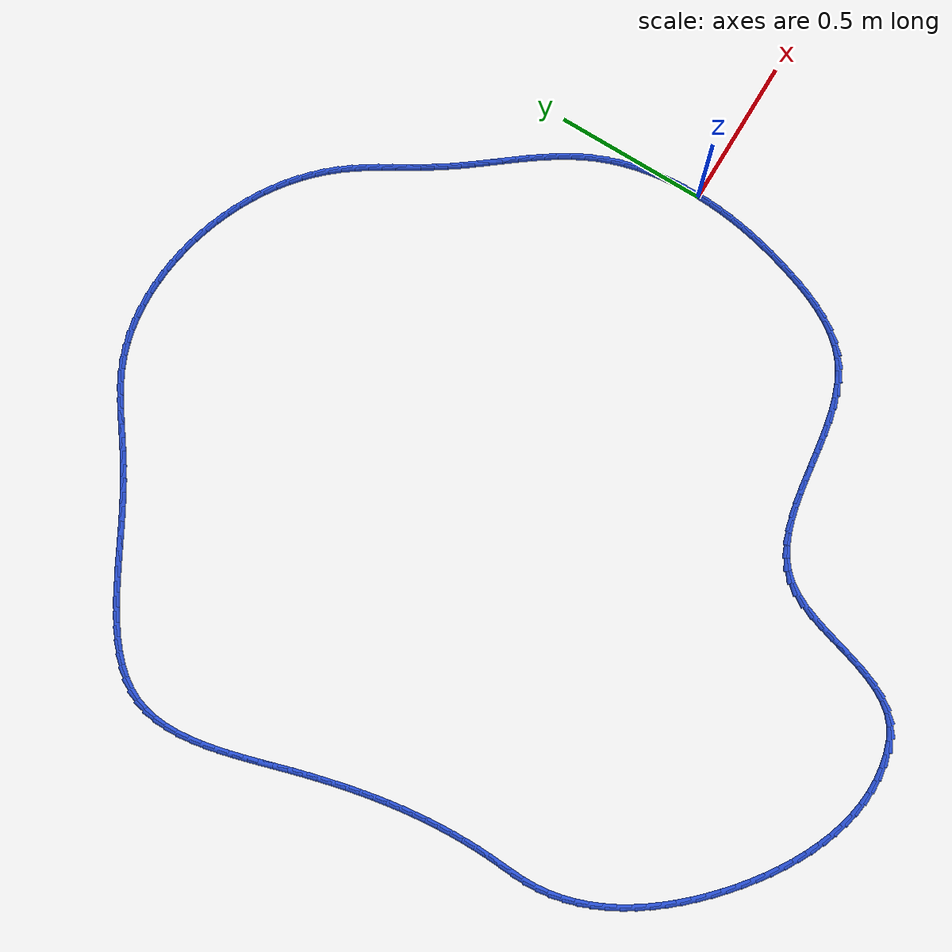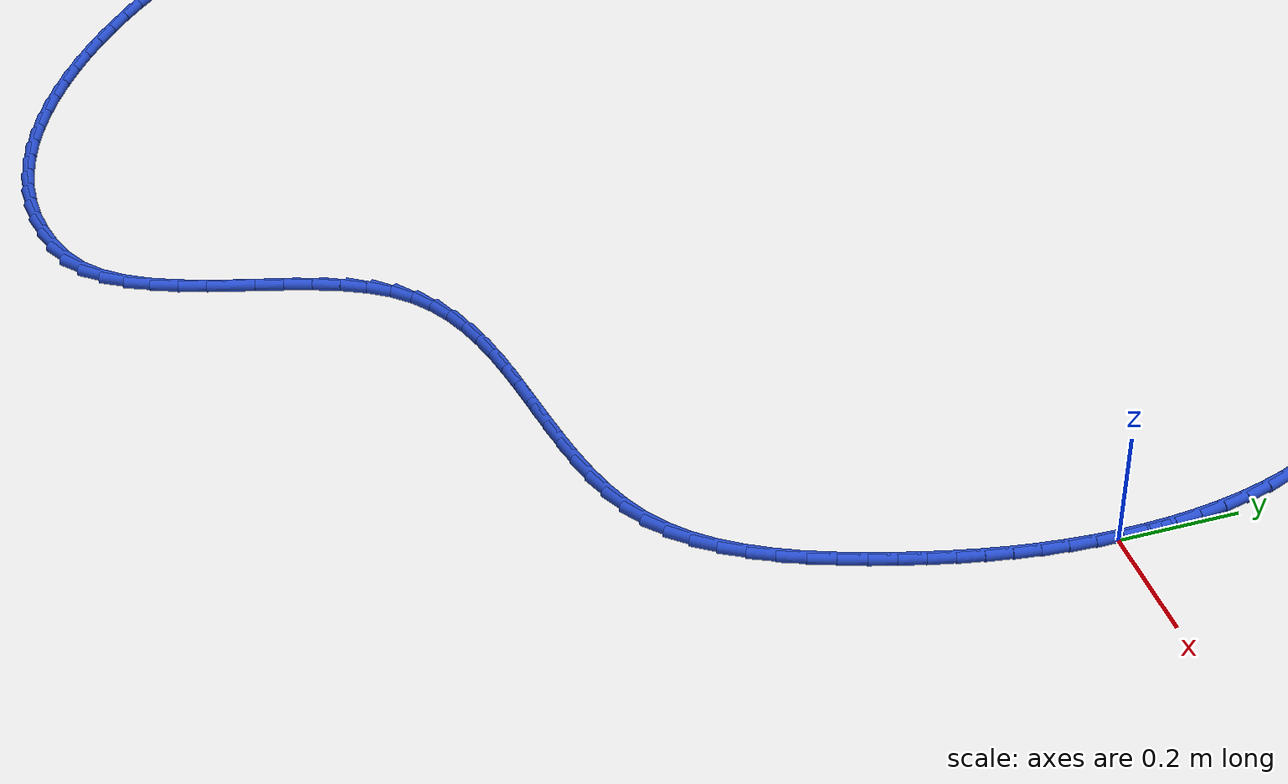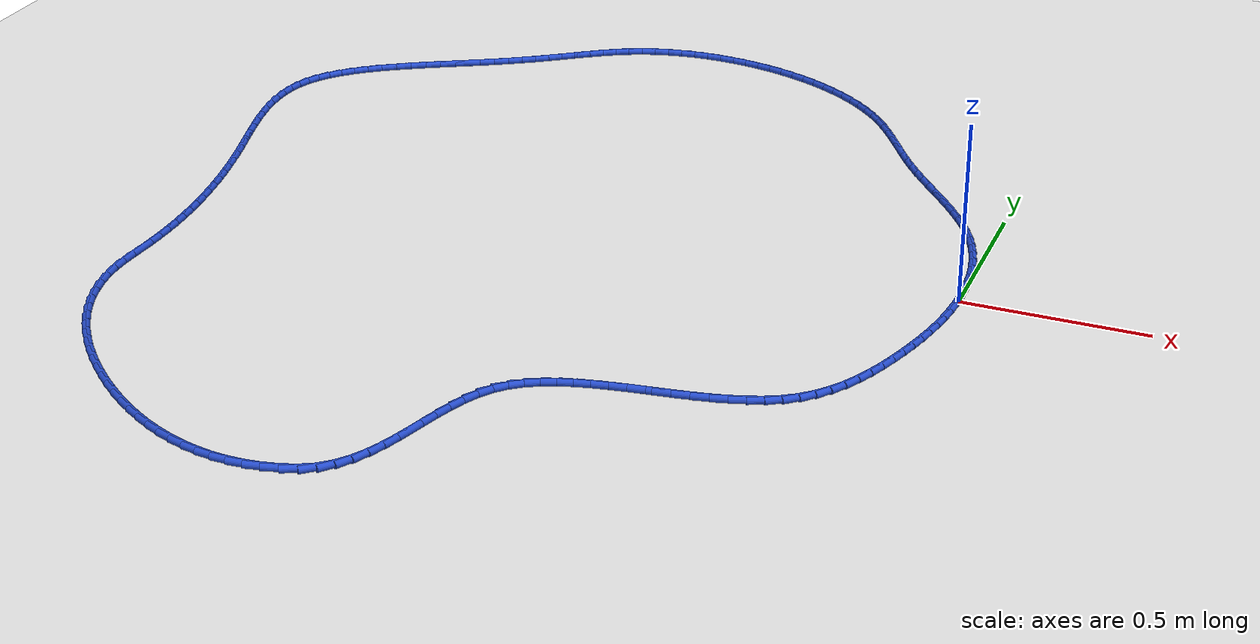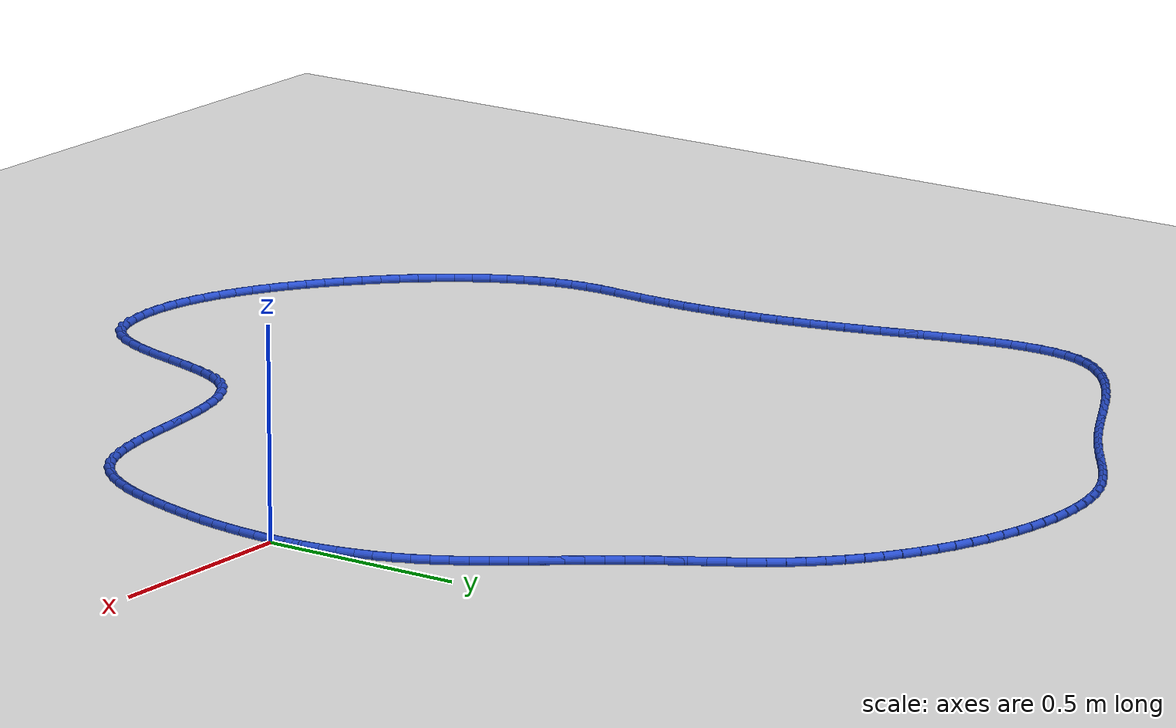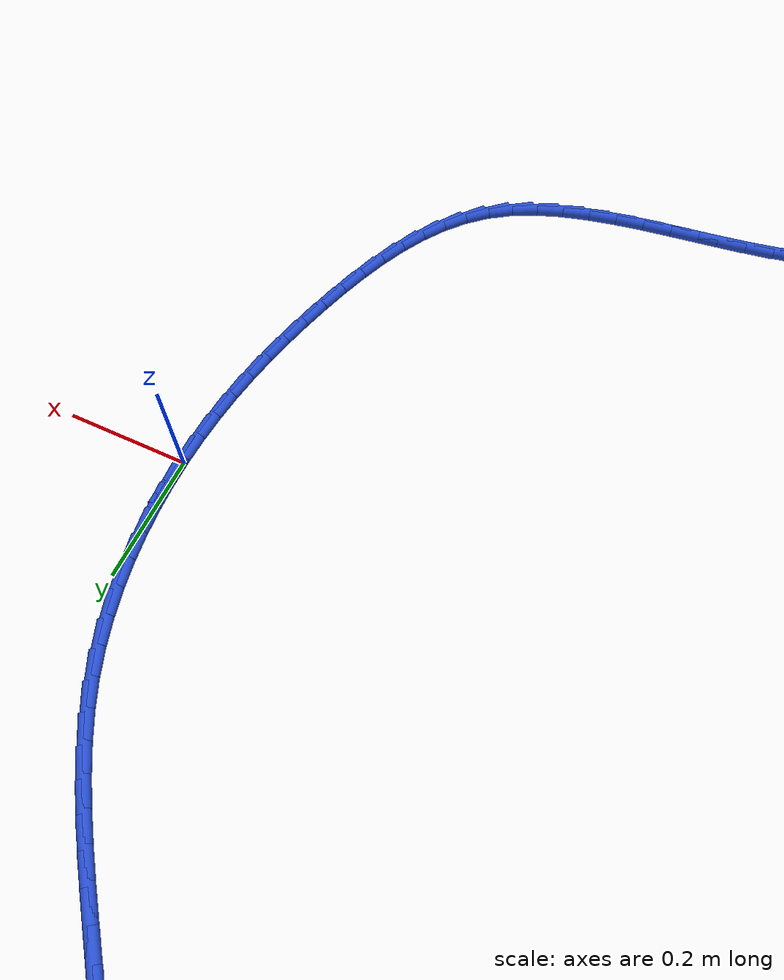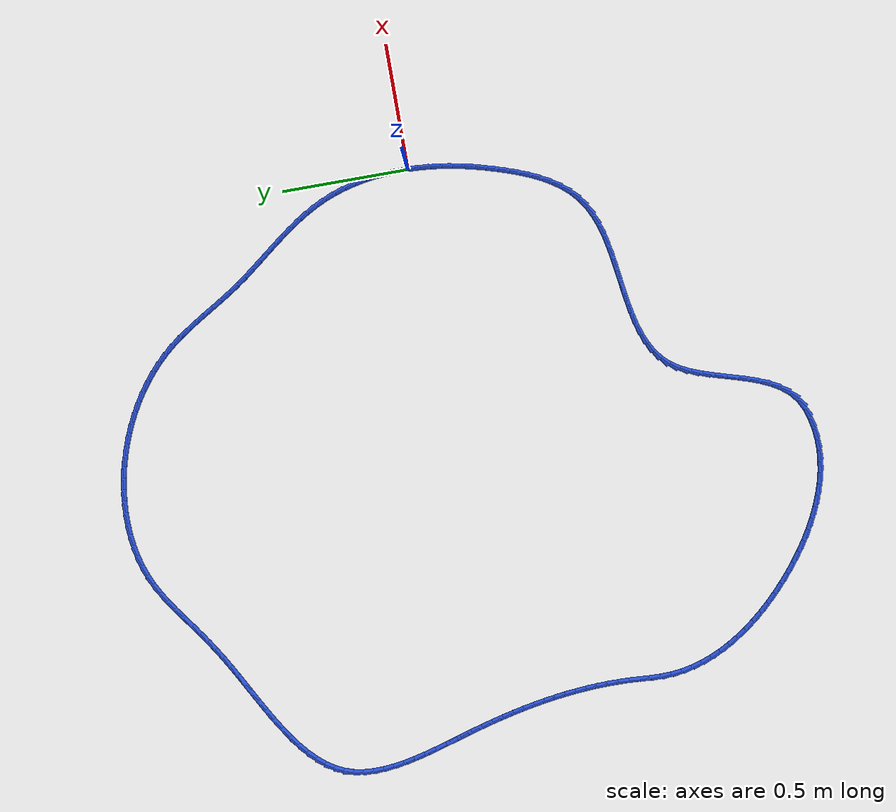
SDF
<sdf version="1.6">
 <world name="default">
  <light name="sun" type="directional">
   <pose>0 0 10 0 -0 0</pose>
   <diffuse>0.8 0.8 0.8 1</diffuse>
   <specular>0.2 0.2 0.2 1</specular>
   <attenuation>
    <range>1000</range>
    <constant>0.9</constant>
    <linear>0.01</linear>
    <quadratic>0.001</quadratic>
   </attenuation>
   <direction>-0.5 0.1 -0.9</direction>
  </light>
  <model name="ground_plane">
   <static>1</static>
   <link name="link">
    <collision name="collision">
     <geometry><plane><normal>0 0 1</normal><size>100 100</size></plane></geometry>
     <surface><friction><ode><mu>100</mu><mu2>50</mu2></ode></friction></surface>
    </collision>
    <visual name="visual">
     <cast_shadows>0</cast_shadows>
     <geometry><plane><normal>0 0 1</normal><size>100 100</size></plane></geometry>
     <material>
      <script><uri>file://media/materials/scripts/gazebo.material</uri><name>Gazebo/WhiteGlow</name></script>
     </material>
    </visual>
   </link>
  </model>
  <gravity>0 0 -9.8</gravity>
  <magnetic_field>6e-06 2.3e-05 -4.2e-05</magnetic_field>
  <atmosphere type="adiabatic"/>
  <physics name="default_physics" default="0" type="ode">
   <max_step_size>0.001</max_step_size>
   <real_time_factor>1</real_time_factor>
   <real_time_update_rate>1000</real_time_update_rate>
  </physics>
  <scene><ambient>0.4 0.4 0.4 1</ambient><background>0.7 0.7 0.7 1</background><shadows>1</shadows></scene>
  <spherical_coordinates>
   <surface_model>EARTH_WGS84</surface_model>
   <latitude_deg>0</latitude_deg>
   <longitude_deg>0</longitude_deg>
   <elevation>0</elevation>
   <heading_deg>0</heading_deg>
  </spherical_coordinates>
  <model name="line">
   <link name="link_0">
    <pose>-2.168404344971009e-17 -2.7755575615628914e-17 0.01 0 1.57 -1.5700291982250192</pose>
    <collision name="collision">
     <geometry><cylinder><radius>0.01</radius><length>0.08</length></cylinder></geometry>
    </collision>
    <visual name="visual">
     <material>
      <script><name>Gazebo/Blue</name><uri>file://media/materials/scripts/gazebo.material</uri></script>
     </material>
     <geometry><cylinder><radius>0.01</radius><length>0.08</length></cylinder></geometry>
    </visual>
   </link>
   <link name="link_1">
    <pose>-3.3373400542923814e-05 0.043504303329024246 0.01 0 1.57 -1.5256582486725725</pose>
    <collision name="collision">
     <geometry><cylinder><radius>0.01</radius><length>0.08</length></cylinder></geometry>
    </collision>
    <visual name="visual">
     <material>
      <script><name>Gazebo/Blue</name><uri>file://media/materials/scripts/gazebo.material</uri></script>
     </material>
     <geometry><cylinder><radius>0.01</radius><length>0.08</length></cylinder></geometry>
    </visual>
   </link>
   <link name="link_2">
    <pose>-0.0020077036784223834 0.08721438833815535 0.01 0 1.57 -1.4792710099667985</pose>
    <collision name="collision">
     <geometry><cylinder><radius>0.01</radius><length>0.08</length></cylinder></geometry>
    </collision>
    <visual name="visual">
     <material>
      <script><name>Gazebo/Blue</name><uri>file://media/materials/scripts/gazebo.material</uri></script>
     </material>
     <geometry><cylinder><radius>0.01</radius><length>0.08</length></cylinder></geometry>
    </visual>
   </link>
   <link name="link_3">
    <pose>-0.006017554612834082 0.13090337112714434 0.01 0 1.57 -1.4303867277252909</pose>
    <collision name="collision">
     <geometry><cylinder><radius>0.01</radius><length>0.08</length></cylinder></geometry>
    </collision>
    <visual name="visual">
     <material>
      <script><name>Gazebo/Blue</name><uri>file://media/materials/scripts/gazebo.material</uri></script>
     </material>
     <geometry><cylinder><radius>0.01</radius><length>0.08</length></cylinder></geometry>
    </visual>
   </link>
   <link name="link_4">
    <pose>-0.012157489982973701 0.17434436779574228 0.01 0 1.57 -1.3785227347976274</pose>
    <collision name="collision">
     <geometry><cylinder><radius>0.01</radius><length>0.08</length></cylinder></geometry>
    </collision>
    <visual name="visual">
     <material>
      <script><name>Gazebo/Blue</name><uri>file://media/materials/scripts/gazebo.material</uri></script>
     </material>
     <geometry><cylinder><radius>0.01</radius><length>0.08</length></cylinder></geometry>
    </visual>
   </link>
   <link name="link_5">
    <pose>-0.020522073568036918 0.2173104944437 0.01 0 1.57 -1.3231982960085122</pose>
    <collision name="collision">
     <geometry><cylinder><radius>0.01</radius><length>0.08</length></cylinder></geometry>
    </collision>
    <visual name="visual">
     <material>
      <script><name>Gazebo/Blue</name><uri>file://media/materials/scripts/gazebo.material</uri></script>
     </material>
     <geometry><cylinder><radius>0.01</radius><length>0.08</length></cylinder></geometry>
    </visual>
   </link>
   <link name="link_6">
    <pose>-0.0312058691472194 0.25957486717076844 0.01 0 1.57 -1.263945834330037</pose>
    <collision name="collision">
     <geometry><cylinder><radius>0.01</radius><length>0.08</length></cylinder></geometry>
    </collision>
    <visual name="visual">
     <material>
      <script><name>Gazebo/Blue</name><uri>file://media/materials/scripts/gazebo.material</uri></script>
     </material>
     <geometry><cylinder><radius>0.01</radius><length>0.08</length></cylinder></geometry>
    </visual>
   </link>
   <link name="link_7">
    <pose>-0.044303440499716844 0.30091060207669873 0.01 0 1.57 -1.2003315872761966</pose>
    <collision name="collision">
     <geometry><cylinder><radius>0.01</radius><length>0.08</length></cylinder></geometry>
    </collision>
    <visual name="visual">
     <material>
      <script><name>Gazebo/Blue</name><uri>file://media/materials/scripts/gazebo.material</uri></script>
     </material>
     <geometry><cylinder><radius>0.01</radius><length>0.08</length></cylinder></geometry>
    </visual>
   </link>
   <link name="link_8">
    <pose>-0.05990935140472492 0.3410908152612417 0.01 0 1.57 -1.1340542222167505</pose>
    <collision name="collision">
     <geometry><cylinder><radius>0.01</radius><length>0.08</length></cylinder></geometry>
    </collision>
    <visual name="visual">
     <material>
      <script><name>Gazebo/Blue</name><uri>file://media/materials/scripts/gazebo.material</uri></script>
     </material>
     <geometry><cylinder><radius>0.01</radius><length>0.08</length></cylinder></geometry>
    </visual>
   </link>
   <link name="link_9">
    <pose>-0.07805070515592961 0.3799534872015394 0.01 0 1.57 -1.0740796577184268</pose>
    <collision name="collision">
     <geometry><cylinder><radius>0.01</radius><length>0.08</length></cylinder></geometry>
    </collision>
    <visual name="visual">
     <material>
      <script><name>Gazebo/Blue</name><uri>file://media/materials/scripts/gazebo.material</uri></script>
     </material>
     <geometry><cylinder><radius>0.01</radius><length>0.08</length></cylinder></geometry>
    </visual>
   </link>
   <link name="link_10">
    <pose>-0.0984650277981196 0.4176150317096617 0.01 0 1.57 -1.0232610814227583</pose>
    <collision name="collision">
     <geometry><cylinder><radius>0.01</radius><length>0.08</length></cylinder></geometry>
    </collision>
    <visual name="visual">
     <material>
      <script><name>Gazebo/Blue</name><uri>file://media/materials/scripts/gazebo.material</uri></script>
     </material>
     <geometry><cylinder><radius>0.01</radius><length>0.08</length></cylinder></geometry>
    </visual>
   </link>
   <link name="link_11">
    <pose>-0.12081216166519879 0.4542665567760833 0.01 0 1.57 -0.9818017492618193</pose>
    <collision name="collision">
     <geometry><cylinder><radius>0.01</radius><length>0.08</length></cylinder></geometry>
    </collision>
    <visual name="visual">
     <material>
      <script><name>Gazebo/Blue</name><uri>file://media/materials/scripts/gazebo.material</uri></script>
     </material>
     <geometry><cylinder><radius>0.01</radius><length>0.08</length></cylinder></geometry>
    </visual>
   </link>
   <link name="link_12">
    <pose>-0.14475194814825101 0.49009917129781655 0.01 0 1.57 -0.9496824390336122</pose>
    <collision name="collision">
     <geometry><cylinder><radius>0.01</radius><length>0.08</length></cylinder></geometry>
    </collision>
    <visual name="visual">
     <material>
      <script><name>Gazebo/Blue</name><uri>file://media/materials/scripts/gazebo.material</uri></script>
     </material>
     <geometry><cylinder><radius>0.01</radius><length>0.08</length></cylinder></geometry>
    </visual>
   </link>
   <link name="link_13">
    <pose>-0.16994422863836023 0.5253039841718733 0.01 0 1.57 -0.926770331393929</pose>
    <collision name="collision">
     <geometry><cylinder><radius>0.01</radius><length>0.08</length></cylinder></geometry>
    </collision>
    <visual name="visual">
     <material>
      <script><name>Gazebo/Blue</name><uri>file://media/materials/scripts/gazebo.material</uri></script>
     </material>
     <geometry><cylinder><radius>0.01</radius><length>0.08</length></cylinder></geometry>
    </visual>
   </link>
   <link name="link_14">
    <pose>-0.1960488445266102 0.5600721042952658 0.01 0 1.57 -0.9129025094839004</pose>
    <collision name="collision">
     <geometry><cylinder><radius>0.01</radius><length>0.08</length></cylinder></geometry>
    </collision>
    <visual name="visual">
     <material>
      <script><name>Gazebo/Blue</name><uri>file://media/materials/scripts/gazebo.material</uri></script>
     </material>
     <geometry><cylinder><radius>0.01</radius><length>0.08</length></cylinder></geometry>
    </visual>
   </link>
   <link name="link_15">
    <pose>-0.22272563720408486 0.5945946405650062 0.01 0 1.57 -0.907942259002747</pose>
    <collision name="collision">
     <geometry><cylinder><radius>0.01</radius><length>0.08</length></cylinder></geometry>
    </collision>
    <visual name="visual">
     <material>
      <script><name>Gazebo/Blue</name><uri>file://media/materials/scripts/gazebo.material</uri></script>
     </material>
     <geometry><cylinder><radius>0.01</radius><length>0.08</length></cylinder></geometry>
    </visual>
   </link>
   <link name="link_16">
    <pose>-0.24963444806186788 0.6290627018781063 0.01 0 1.57 -0.9118107428308672</pose>
    <collision name="collision">
     <geometry><cylinder><radius>0.01</radius><length>0.08</length></cylinder></geometry>
    </collision>
    <visual name="visual">
     <material>
      <script><name>Gazebo/Blue</name><uri>file://media/materials/scripts/gazebo.material</uri></script>
     </material>
     <geometry><cylinder><radius>0.01</radius><length>0.08</length></cylinder></geometry>
    </visual>
   </link>
   <link name="link_17">
    <pose>-0.2764351184910433 0.6636673971315784 0.01 0 1.57 -0.924497199518245</pose>
    <collision name="collision">
     <geometry><cylinder><radius>0.01</radius><length>0.08</length></cylinder></geometry>
    </collision>
    <visual name="visual">
     <material>
      <script><name>Gazebo/Blue</name><uri>file://media/materials/scripts/gazebo.material</uri></script>
     </material>
     <geometry><cylinder><radius>0.01</radius><length>0.08</length></cylinder></geometry>
    </visual>
   </link>
   <link name="link_18">
    <pose>-0.30278748988269505 0.698599835222435 0.01 0 1.57 -0.9460494154251001</pose>
    <collision name="collision">
     <geometry><cylinder><radius>0.01</radius><length>0.08</length></cylinder></geometry>
    </collision>
    <visual name="visual">
     <material>
      <script><name>Gazebo/Blue</name><uri>file://media/materials/scripts/gazebo.material</uri></script>
     </material>
     <geometry><cylinder><radius>0.01</radius><length>0.08</length></cylinder></geometry>
    </visual>
   </link>
   <link name="link_19">
    <pose>-0.3283514036279067 0.7340511250476873 0.01 0 1.57 -0.9762403263146235</pose>
    <collision name="collision">
     <geometry><cylinder><radius>0.01</radius><length>0.08</length></cylinder></geometry>
    </collision>
    <visual name="visual">
     <material>
      <script><name>Gazebo/Blue</name><uri>file://media/materials/scripts/gazebo.material</uri></script>
     </material>
     <geometry><cylinder><radius>0.01</radius><length>0.08</length></cylinder></geometry>
    </visual>
   </link>
   <link name="link_20">
    <pose>-0.3527978623639285 0.7702052004127573 0.01 0 1.57 -1.0057383517148377</pose>
    <collision name="collision">
     <geometry><cylinder><radius>0.01</radius><length>0.08</length></cylinder></geometry>
    </collision>
    <visual name="visual">
     <material>
      <script><name>Gazebo/Blue</name><uri>file://media/materials/scripts/gazebo.material</uri></script>
     </material>
     <geometry><cylinder><radius>0.01</radius><length>0.08</length></cylinder></geometry>
    </visual>
   </link>
   <link name="link_21">
    <pose>-0.3761420955931035 0.8070247062769662 0.01 0 1.57 -1.023588888113034</pose>
    <collision name="collision">
     <geometry><cylinder><radius>0.01</radius><length>0.08</length></cylinder></geometry>
    </collision>
    <visual name="visual">
     <material>
      <script><name>Gazebo/Blue</name><uri>file://media/materials/scripts/gazebo.material</uri></script>
     </material>
     <geometry><cylinder><radius>0.01</radius><length>0.08</length></cylinder></geometry>
    </visual>
   </link>
   <link name="link_22">
    <pose>-0.39880059905364457 0.8442143305622332 0.01 0 1.57 -1.0291538361993628</pose>
    <collision name="collision">
     <geometry><cylinder><radius>0.01</radius><length>0.08</length></cylinder></geometry>
    </collision>
    <visual name="visual">
     <material>
      <script><name>Gazebo/Blue</name><uri>file://media/materials/scripts/gazebo.material</uri></script>
     </material>
     <geometry><cylinder><radius>0.01</radius><length>0.08</length></cylinder></geometry>
    </visual>
   </link>
   <link name="link_23">
    <pose>-0.4212125217384484 0.8814641983742126 0.01 0 1.57 -1.0223800508573053</pose>
    <collision name="collision">
     <geometry><cylinder><radius>0.01</radius><length>0.08</length></cylinder></geometry>
    </collision>
    <visual name="visual">
     <material>
      <script><name>Gazebo/Blue</name><uri>file://media/materials/scripts/gazebo.material</uri></script>
     </material>
     <geometry><cylinder><radius>0.01</radius><length>0.08</length></cylinder></geometry>
    </visual>
   </link>
   <link name="link_24">
    <pose>-0.44381701264041185 0.9184644348185598 0.01 0 1.57 -1.0031564145811875</pose>
    <collision name="collision">
     <geometry><cylinder><radius>0.01</radius><length>0.08</length></cylinder></geometry>
    </collision>
    <visual name="visual">
     <material>
      <script><name>Gazebo/Blue</name><uri>file://media/materials/scripts/gazebo.material</uri></script>
     </material>
     <geometry><cylinder><radius>0.01</radius><length>0.08</length></cylinder></geometry>
    </visual>
   </link>
   <link name="link_25">
    <pose>-0.46705322075243166 0.954905165000929 0.01 0 1.57 -0.9713441138166472</pose>
    <collision name="collision">
     <geometry><cylinder><radius>0.01</radius><length>0.08</length></cylinder></geometry>
    </collision>
    <visual name="visual">
     <material>
      <script><name>Gazebo/Blue</name><uri>file://media/materials/scripts/gazebo.material</uri></script>
     </material>
     <geometry><cylinder><radius>0.01</radius><length>0.08</length></cylinder></geometry>
    </visual>
   </link>
   <link name="link_26">
    <pose>-0.4913602950674047 0.9904765140269751 0.01 0 1.57 -0.9268669821839701</pose>
    <collision name="collision">
     <geometry><cylinder><radius>0.01</radius><length>0.08</length></cylinder></geometry>
    </collision>
    <visual name="visual">
     <material>
      <script><name>Gazebo/Blue</name><uri>file://media/materials/scripts/gazebo.material</uri></script>
     </material>
     <geometry><cylinder><radius>0.01</radius><length>0.08</length></cylinder></geometry>
    </visual>
   </link>
   <link name="link_27">
    <pose>-0.5171773845782278 1.024868607002353 0.01 0 1.57 -0.8701325529390257</pose>
    <collision name="collision">
     <geometry><cylinder><radius>0.01</radius><length>0.08</length></cylinder></geometry>
    </collision>
    <visual name="visual">
     <material>
      <script><name>Gazebo/Blue</name><uri>file://media/materials/scripts/gazebo.material</uri></script>
     </material>
     <geometry><cylinder><radius>0.01</radius><length>0.08</length></cylinder></geometry>
    </visual>
   </link>
   <link name="link_28">
    <pose>-0.5449326961752677 1.0577765173266243 0.01 0 1.57 -0.8081801863817377</pose>
    <collision name="collision">
     <geometry><cylinder><radius>0.01</radius><length>0.08</length></cylinder></geometry>
    </collision>
    <visual name="visual">
     <material>
      <script><name>Gazebo/Blue</name><uri>file://media/materials/scripts/gazebo.material</uri></script>
     </material>
     <geometry><cylinder><radius>0.01</radius><length>0.08</length></cylinder></geometry>
    </visual>
   </link>
   <link name="link_29">
    <pose>-0.5747824612413662 1.0890183125627728 0.01 0 1.57 -0.7480066415759706</pose>
    <collision name="collision">
     <geometry><cylinder><radius>0.01</radius><length>0.08</length></cylinder></geometry>
    </collision>
    <visual name="visual">
     <material>
      <script><name>Gazebo/Blue</name><uri>file://media/materials/scripts/gazebo.material</uri></script>
     </material>
     <geometry><cylinder><radius>0.01</radius><length>0.08</length></cylinder></geometry>
    </visual>
   </link>
   <link name="link_30">
    <pose>-0.6065991513762627 1.11854038358294 0.01 0 1.57 -0.6897903795208525</pose>
    <collision name="collision">
     <geometry><cylinder><radius>0.01</radius><length>0.08</length></cylinder></geometry>
    </collision>
    <visual name="visual">
     <material>
      <script><name>Gazebo/Blue</name><uri>file://media/materials/scripts/gazebo.material</uri></script>
     </material>
     <geometry><cylinder><radius>0.01</radius><length>0.08</length></cylinder></geometry>
    </visual>
   </link>
   <link name="link_31">
    <pose>-0.6402419378927278 1.146295135983475 0.01 0 1.57 -0.6333486373392374</pose>
    <collision name="collision">
     <geometry><cylinder><radius>0.01</radius><length>0.08</length></cylinder></geometry>
    </collision>
    <visual name="visual">
     <material>
      <script><name>Gazebo/Blue</name><uri>file://media/materials/scripts/gazebo.material</uri></script>
     </material>
     <geometry><cylinder><radius>0.01</radius><length>0.08</length></cylinder></geometry>
    </visual>
   </link>
   <link name="link_32">
    <pose>-0.6755699921035327 1.1722349753607268 0.01 0 1.57 -0.5784735718401259</pose>
    <collision name="collision">
     <geometry><cylinder><radius>0.01</radius><length>0.08</length></cylinder></geometry>
    </collision>
    <visual name="visual">
     <material>
      <script><name>Gazebo/Blue</name><uri>file://media/materials/scripts/gazebo.material</uri></script>
     </material>
     <geometry><cylinder><radius>0.01</radius><length>0.08</length></cylinder></geometry>
    </visual>
   </link>
   <link name="link_33">
    <pose>-0.7124424853214479 1.1963123073110435 0.01 0 1.57 -0.5249401805187072</pose>
    <collision name="collision">
     <geometry><cylinder><radius>0.01</radius><length>0.08</length></cylinder></geometry>
    </collision>
    <visual name="visual">
     <material>
      <script><name>Gazebo/Blue</name><uri>file://media/materials/scripts/gazebo.material</uri></script>
     </material>
     <geometry><cylinder><radius>0.01</radius><length>0.08</length></cylinder></geometry>
    </visual>
   </link>
   <link name="link_34">
    <pose>-0.7507185888592446 1.2184795374307749 0.01 0 1.57 -0.4725123833153278</pose>
    <collision name="collision">
     <geometry><cylinder><radius>0.01</radius><length>0.08</length></cylinder></geometry>
    </collision>
    <visual name="visual">
     <material>
      <script><name>Gazebo/Blue</name><uri>file://media/materials/scripts/gazebo.material</uri></script>
     </material>
     <geometry><cylinder><radius>0.01</radius><length>0.08</length></cylinder></geometry>
    </visual>
   </link>
   <link name="link_35">
    <pose>-0.7902574740296934 1.2386890713162695 0.01 0 1.57 -0.4209475074292948</pose>
    <collision name="collision">
     <geometry><cylinder><radius>0.01</radius><length>0.08</length></cylinder></geometry>
    </collision>
    <visual name="visual">
     <material>
      <script><name>Gazebo/Blue</name><uri>file://media/materials/scripts/gazebo.material</uri></script>
     </material>
     <geometry><cylinder><radius>0.01</radius><length>0.08</length></cylinder></geometry>
    </visual>
   </link>
   <link name="link_36">
    <pose>-0.8309183121455652 1.2568933145638763 0.01 0 1.57 -0.36999947861142113</pose>
    <collision name="collision">
     <geometry><cylinder><radius>0.01</radius><length>0.08</length></cylinder></geometry>
    </collision>
    <visual name="visual">
     <material>
      <script><name>Gazebo/Blue</name><uri>file://media/materials/scripts/gazebo.material</uri></script>
     </material>
     <geometry><cylinder><radius>0.01</radius><length>0.08</length></cylinder></geometry>
    </visual>
   </link>
   <link name="link_37">
    <pose>-0.872560274519631 1.2730446727699443 0.01 0 1.57 -0.3194210382520062</pose>
    <collision name="collision">
     <geometry><cylinder><radius>0.01</radius><length>0.08</length></cylinder></geometry>
    </collision>
    <visual name="visual">
     <material>
      <script><name>Gazebo/Blue</name><uri>file://media/materials/scripts/gazebo.material</uri></script>
     </material>
     <geometry><cylinder><radius>0.01</radius><length>0.08</length></cylinder></geometry>
    </visual>
   </link>
   <link name="link_38">
    <pose>-0.9150425324646615 1.287095551530822 0.01 0 1.57 -0.2689652978305768</pose>
    <collision name="collision">
     <geometry><cylinder><radius>0.01</radius><length>0.08</length></cylinder></geometry>
    </collision>
    <visual name="visual">
     <material>
      <script><name>Gazebo/Blue</name><uri>file://media/materials/scripts/gazebo.material</uri></script>
     </material>
     <geometry><cylinder><radius>0.01</radius><length>0.08</length></cylinder></geometry>
    </visual>
   </link>
   <link name="link_39">
    <pose>-0.9582242572934281 1.298998356442859 0.01 0 1.57 -0.21838692591371678</pose>
    <collision name="collision">
     <geometry><cylinder><radius>0.01</radius><length>0.08</length></cylinder></geometry>
    </collision>
    <visual name="visual">
     <material>
      <script><name>Gazebo/Blue</name><uri>file://media/materials/scripts/gazebo.material</uri></script>
     </material>
     <geometry><cylinder><radius>0.01</radius><length>0.08</length></cylinder></geometry>
    </visual>
   </link>
   <link name="link_40">
    <pose>-1.001964620318701 1.3087054931024038 0.01 0 1.57 -0.1674371363741824</pose>
    <collision name="collision">
     <geometry><cylinder><radius>0.01</radius><length>0.08</length></cylinder></geometry>
    </collision>
    <visual name="visual">
     <material>
      <script><name>Gazebo/Blue</name><uri>file://media/materials/scripts/gazebo.material</uri></script>
     </material>
     <geometry><cylinder><radius>0.01</radius><length>0.08</length></cylinder></geometry>
    </visual>
   </link>
   <link name="link_41">
    <pose>-1.046122514006533 1.3161690424302528 0.01 0 1.57 -0.11538436155777022</pose>
    <collision name="collision">
     <geometry><cylinder><radius>0.01</radius><length>0.08</length></cylinder></geometry>
    </collision>
    <visual name="visual">
     <material>
      <script><name>Gazebo/Blue</name><uri>file://media/materials/scripts/gazebo.material</uri></script>
     </material>
     <geometry><cylinder><radius>0.01</radius><length>0.08</length></cylinder></geometry>
    </visual>
   </link>
   <link name="link_42">
    <pose>-1.0905357112680854 1.3213164947649487 0.01 0 1.57 -0.061030810334161884</pose>
    <collision name="collision">
     <geometry><cylinder><radius>0.01</radius><length>0.08</length></cylinder></geometry>
    </collision>
    <visual name="visual">
     <material>
      <script><name>Gazebo/Blue</name><uri>file://media/materials/scripts/gazebo.material</uri></script>
     </material>
     <geometry><cylinder><radius>0.01</radius><length>0.08</length></cylinder></geometry>
    </visual>
   </link>
   <link name="link_43">
    <pose>-1.1350064405579257 1.32403395420901 0.01 0 1.57 -0.003826057197478869</pose>
    <collision name="collision">
     <geometry><cylinder><radius>0.01</radius><length>0.08</length></cylinder></geometry>
    </collision>
    <visual name="visual">
     <material>
      <script><name>Gazebo/Blue</name><uri>file://media/materials/scripts/gazebo.material</uri></script>
     </material>
     <geometry><cylinder><radius>0.01</radius><length>0.08</length></cylinder></geometry>
    </visual>
   </link>
   <link name="link_44">
    <pose>-1.1793335190831997 1.324203552974415 0.01 0 1.57 0.05669230682256397</pose>
    <collision name="collision">
     <geometry><cylinder><radius>0.01</radius><length>0.08</length></cylinder></geometry>
    </collision>
    <visual name="visual">
     <material>
      <script><name>Gazebo/Blue</name><uri>file://media/materials/scripts/gazebo.material</uri></script>
     </material>
     <geometry><cylinder><radius>0.01</radius><length>0.08</length></cylinder></geometry>
    </visual>
   </link>
   <link name="link_45">
    <pose>-1.2233157640510541 1.32170742327314 0.01 0 1.57 0.12095782961880742</pose>
    <collision name="collision">
     <geometry><cylinder><radius>0.01</radius><length>0.08</length></cylinder></geometry>
    </collision>
    <visual name="visual">
     <material>
      <script><name>Gazebo/Blue</name><uri>file://media/materials/scripts/gazebo.material</uri></script>
     </material>
     <geometry><cylinder><radius>0.01</radius><length>0.08</length></cylinder></geometry>
    </visual>
   </link>
   <link name="link_46">
    <pose>-1.2667519926686353 1.3164276973171631 0.01 0 1.57 0.18935030209173057</pose>
    <collision name="collision">
     <geometry><cylinder><radius>0.01</radius><length>0.08</length></cylinder></geometry>
    </collision>
    <visual name="visual">
     <material>
      <script><name>Gazebo/Blue</name><uri>file://media/materials/scripts/gazebo.material</uri></script>
     </material>
     <geometry><cylinder><radius>0.01</radius><length>0.08</length></cylinder></geometry>
    </visual>
   </link>
   <link name="link_47">
    <pose>-1.309441022143088 1.308246507318462 0.01 0 1.57 0.2621603259520876</pose>
    <collision name="collision">
     <geometry><cylinder><radius>0.01</radius><length>0.08</length></cylinder></geometry>
    </collision>
    <visual name="visual">
     <material>
      <script><name>Gazebo/Blue</name><uri>file://media/materials/scripts/gazebo.material</uri></script>
     </material>
     <geometry><cylinder><radius>0.01</radius><length>0.08</length></cylinder></geometry>
    </visual>
   </link>
   <link name="link_48">
    <pose>-1.351181669681559 1.2970459854890126 0.01 0 1.57 0.3395435796622505</pose>
    <collision name="collision">
     <geometry><cylinder><radius>0.01</radius><length>0.08</length></cylinder></geometry>
    </collision>
    <visual name="visual">
     <material>
      <script><name>Gazebo/Blue</name><uri>file://media/materials/scripts/gazebo.material</uri></script>
     </material>
     <geometry><cylinder><radius>0.01</radius><length>0.08</length></cylinder></geometry>
    </visual>
   </link>
   <link name="link_49">
    <pose>-1.3917727524911951 1.2827082640407936 0.01 0 1.57 0.42093712263266997</pose>
    <collision name="collision">
     <geometry><cylinder><radius>0.01</radius><length>0.08</length></cylinder></geometry>
    </collision>
    <visual name="visual">
     <material>
      <script><name>Gazebo/Blue</name><uri>file://media/materials/scripts/gazebo.material</uri></script>
     </material>
     <geometry><cylinder><radius>0.01</radius><length>0.08</length></cylinder></geometry>
    </visual>
   </link>
   <link name="link_50">
    <pose>-1.431024405599243 1.2651354156227603 0.01 0 1.57 0.49559298672273483</pose>
    <collision name="collision">
     <geometry><cylinder><radius>0.01</radius><length>0.08</length></cylinder></geometry>
    </collision>
    <visual name="visual">
     <material>
      <script><name>Gazebo/Blue</name><uri>file://media/materials/scripts/gazebo.material</uri></script>
     </material>
     <geometry><cylinder><radius>0.01</radius><length>0.08</length></cylinder></geometry>
    </visual>
   </link>
   <link name="link_51">
    <pose>-1.4689697541416944 1.2446223906792553 0.01 0 1.57 0.5537315926731041</pose>
    <collision name="collision">
     <geometry><cylinder><radius>0.01</radius><length>0.08</length></cylinder></geometry>
    </collision>
    <visual name="visual">
     <material>
      <script><name>Gazebo/Blue</name><uri>file://media/materials/scripts/gazebo.material</uri></script>
     </material>
     <geometry><cylinder><radius>0.01</radius><length>0.08</length></cylinder></geometry>
    </visual>
   </link>
   <link name="link_52">
    <pose>-1.5058459617517588 1.2218236273261294 0.01 0 1.57 0.5953084457364575</pose>
    <collision name="collision">
     <geometry><cylinder><radius>0.01</radius><length>0.08</length></cylinder></geometry>
    </collision>
    <visual name="visual">
     <material>
      <script><name>Gazebo/Blue</name><uri>file://media/materials/scripts/gazebo.material</uri></script>
     </material>
     <geometry><cylinder><radius>0.01</radius><length>0.08</length></cylinder></geometry>
    </visual>
   </link>
   <link name="link_53">
    <pose>-1.5418977101846243 1.1974068095725383 0.01 0 1.57 0.6208105087612137</pose>
    <collision name="collision">
     <geometry><cylinder><radius>0.01</radius><length>0.08</length></cylinder></geometry>
    </collision>
    <visual name="visual">
     <material>
      <script><name>Gazebo/Blue</name><uri>file://media/materials/scripts/gazebo.material</uri></script>
     </material>
     <geometry><cylinder><radius>0.01</radius><length>0.08</length></cylinder></geometry>
    </visual>
   </link>
   <link name="link_54">
    <pose>-1.5773696811954772 1.1720396214276338 0.01 0 1.57 0.6305769314997918</pose>
    <collision name="collision">
     <geometry><cylinder><radius>0.01</radius><length>0.08</length></cylinder></geometry>
    </collision>
    <visual name="visual">
     <material>
      <script><name>Gazebo/Blue</name><uri>file://media/materials/scripts/gazebo.material</uri></script>
     </material>
     <geometry><cylinder><radius>0.01</radius><length>0.08</length></cylinder></geometry>
    </visual>
   </link>
   <link name="link_55">
    <pose>-1.612506556539506 1.1463897469005704 0.01 0 1.57 0.624615673662241</pose>
    <collision name="collision">
     <geometry><cylinder><radius>0.01</radius><length>0.08</length></cylinder></geometry>
    </collision>
    <visual name="visual">
     <material>
      <script><name>Gazebo/Blue</name><uri>file://media/materials/scripts/gazebo.material</uri></script>
     </material>
     <geometry><cylinder><radius>0.01</radius><length>0.08</length></cylinder></geometry>
    </visual>
   </link>
   <link name="link_56">
    <pose>-1.6475530349599123 1.1211247329157865 0.01 0 1.57 0.6058468612660123</pose>
    <collision name="collision">
     <geometry><cylinder><radius>0.01</radius><length>0.08</length></cylinder></geometry>
    </collision>
    <visual name="visual">
     <material>
      <script><name>Gazebo/Blue</name><uri>file://media/materials/scripts/gazebo.material</uri></script>
     </material>
     <geometry><cylinder><radius>0.01</radius><length>0.08</length></cylinder></geometry>
    </visual>
   </link>
   <link name="link_57">
    <pose>-1.6827772542499968 1.096722985087023 0.01 0 1.57 0.5840741859471246</pose>
    <collision name="collision">
     <geometry><cylinder><radius>0.01</radius><length>0.08</length></cylinder></geometry>
    </collision>
    <visual name="visual">
     <material>
      <script><name>Gazebo/Blue</name><uri>file://media/materials/scripts/gazebo.material</uri></script>
     </material>
     <geometry><cylinder><radius>0.01</radius><length>0.08</length></cylinder></geometry>
    </visual>
   </link>
   <link name="link_58">
    <pose>-1.7185172870066328 1.0730985704410467 0.01 0 1.57 0.5617065692769106</pose>
    <collision name="collision">
     <geometry><cylinder><radius>0.01</radius><length>0.08</length></cylinder></geometry>
    </collision>
    <visual name="visual">
     <material>
      <script><name>Gazebo/Blue</name><uri>file://media/materials/scripts/gazebo.material</uri></script>
     </material>
     <geometry><cylinder><radius>0.01</radius><length>0.08</length></cylinder></geometry>
    </visual>
   </link>
   <link name="link_59">
    <pose>-1.755124191592309 1.0500607674266496 0.01 0 1.57 0.539388807184973</pose>
    <collision name="collision">
     <geometry><cylinder><radius>0.01</radius><length>0.08</length></cylinder></geometry>
    </collision>
    <visual name="visual">
     <material>
      <script><name>Gazebo/Blue</name><uri>file://media/materials/scripts/gazebo.material</uri></script>
     </material>
     <geometry><cylinder><radius>0.01</radius><length>0.08</length></cylinder></geometry>
    </visual>
   </link>
   <link name="link_60">
    <pose>-1.7929490263695147 1.0274188544926226 0.01 0 1.57 0.5186388453061893</pose>
    <collision name="collision">
     <geometry><cylinder><radius>0.01</radius><length>0.08</length></cylinder></geometry>
    </collision>
    <visual name="visual">
     <material>
      <script><name>Gazebo/Blue</name><uri>file://media/materials/scripts/gazebo.material</uri></script>
     </material>
     <geometry><cylinder><radius>0.01</radius><length>0.08</length></cylinder></geometry>
    </visual>
   </link>
   <link name="link_61">
    <pose>-1.8322538622166253 1.0049853891619354 0.01 0 1.57 0.5050150374955464</pose>
    <collision name="collision">
     <geometry><cylinder><radius>0.01</radius><length>0.08</length></cylinder></geometry>
    </collision>
    <visual name="visual">
     <material>
      <script><name>Gazebo/Blue</name><uri>file://media/materials/scripts/gazebo.material</uri></script>
     </material>
     <geometry><cylinder><radius>0.01</radius><length>0.08</length></cylinder></geometry>
    </visual>
   </link>
   <link name="link_62">
    <pose>-1.872758908106407 0.9825928958708826 0.01 0 1.57 0.49985176683955396</pose>
    <collision name="collision">
     <geometry><cylinder><radius>0.01</radius><length>0.08</length></cylinder></geometry>
    </collision>
    <visual name="visual">
     <material>
      <script><name>Gazebo/Blue</name><uri>file://media/materials/scripts/gazebo.material</uri></script>
     </material>
     <geometry><cylinder><radius>0.01</radius><length>0.08</length></cylinder></geometry>
    </visual>
   </link>
   <link name="link_63">
    <pose>-1.9139804204021162 0.9600814144467359 0.01 0 1.57 0.5026726263491614</pose>
    <collision name="collision">
     <geometry><cylinder><radius>0.01</radius><length>0.08</length></cylinder></geometry>
    </collision>
    <visual name="visual">
     <material>
      <script><name>Gazebo/Blue</name><uri>file://media/materials/scripts/gazebo.material</uri></script>
     </material>
     <geometry><cylinder><radius>0.01</radius><length>0.08</length></cylinder></geometry>
    </visual>
   </link>
   <link name="link_64">
    <pose>-1.955434285334234 0.9372909983556854 0.01 0 1.57 0.5133681828867818</pose>
    <collision name="collision">
     <geometry><cylinder><radius>0.01</radius><length>0.08</length></cylinder></geometry>
    </collision>
    <visual name="visual">
     <material>
      <script><name>Gazebo/Blue</name><uri>file://media/materials/scripts/gazebo.material</uri></script>
     </material>
     <geometry><cylinder><radius>0.01</radius><length>0.08</length></cylinder></geometry>
    </visual>
   </link>
   <link name="link_65">
    <pose>-1.9966363891332402 0.9140617010639187 0.01 0 1.57 0.5321730342734662</pose>
    <collision name="collision">
     <geometry><cylinder><radius>0.01</radius><length>0.08</length></cylinder></geometry>
    </collision>
    <visual name="visual">
     <material>
      <script><name>Gazebo/Blue</name><uri>file://media/materials/scripts/gazebo.material</uri></script>
     </material>
     <geometry><cylinder><radius>0.01</radius><length>0.08</length></cylinder></geometry>
    </visual>
   </link>
   <link name="link_66">
    <pose>-2.037102618029618 0.8902335760376248 0.01 0 1.57 0.5596613166465336</pose>
    <collision name="collision">
     <geometry><cylinder><radius>0.01</radius><length>0.08</length></cylinder></geometry>
    </collision>
    <visual name="visual">
     <material>
      <script><name>Gazebo/Blue</name><uri>file://media/materials/scripts/gazebo.material</uri></script>
     </material>
     <geometry><cylinder><radius>0.01</radius><length>0.08</length></cylinder></geometry>
    </visual>
   </link>
   <link name="link_67">
    <pose>-2.0763488582538474 0.8656466767429926 0.01 0 1.57 0.596756995318464</pose>
    <collision name="collision">
     <geometry><cylinder><radius>0.01</radius><length>0.08</length></cylinder></geometry>
    </collision>
    <visual name="visual">
     <material>
      <script><name>Gazebo/Blue</name><uri>file://media/materials/scripts/gazebo.material</uri></script>
     </material>
     <geometry><cylinder><radius>0.01</radius><length>0.08</length></cylinder></geometry>
    </visual>
   </link>
   <link name="link_68">
    <pose>-2.1138909960364094 0.8401410566462101 0.01 0 1.57 0.6447462445790583</pose>
    <collision name="collision">
     <geometry><cylinder><radius>0.01</radius><length>0.08</length></cylinder></geometry>
    </collision>
    <visual name="visual">
     <material>
      <script><name>Gazebo/Blue</name><uri>file://media/materials/scripts/gazebo.material</uri></script>
     </material>
     <geometry><cylinder><radius>0.01</radius><length>0.08</length></cylinder></geometry>
    </visual>
   </link>
   <link name="link_69">
    <pose>-2.149244917607786 0.8135567692134663 0.01 0 1.57 0.7052671447336795</pose>
    <collision name="collision">
     <geometry><cylinder><radius>0.01</radius><length>0.08</length></cylinder></geometry>
    </collision>
    <visual name="visual">
     <material>
      <script><name>Gazebo/Blue</name><uri>file://media/materials/scripts/gazebo.material</uri></script>
     </material>
     <geometry><cylinder><radius>0.01</radius><length>0.08</length></cylinder></geometry>
    </visual>
   </link>
   <link name="link_70">
    <pose>-2.181926509198458 0.7857338679109501 0.01 0 1.57 0.7802287854264223</pose>
    <collision name="collision">
     <geometry><cylinder><radius>0.01</radius><length>0.08</length></cylinder></geometry>
    </collision>
    <visual name="visual">
     <material>
      <script><name>Gazebo/Blue</name><uri>file://media/materials/scripts/gazebo.material</uri></script>
     </material>
     <geometry><cylinder><radius>0.01</radius><length>0.08</length></cylinder></geometry>
    </visual>
   </link>
   <link name="link_71">
    <pose>-2.2114516570389067 0.7565124062048496 0.01 0 1.57 0.8715764304216828</pose>
    <collision name="collision">
     <geometry><cylinder><radius>0.01</radius><length>0.08</length></cylinder></geometry>
    </collision>
    <visual name="visual">
     <material>
      <script><name>Gazebo/Blue</name><uri>file://media/materials/scripts/gazebo.material</uri></script>
     </material>
     <geometry><cylinder><radius>0.01</radius><length>0.08</length></cylinder></geometry>
    </visual>
   </link>
   <link name="link_72">
    <pose>-2.237336247359613 0.7257324375613539 0.01 0 1.57 0.9807874666371675</pose>
    <collision name="collision">
     <geometry><cylinder><radius>0.01</radius><length>0.08</length></cylinder></geometry>
    </collision>
    <visual name="visual">
     <material>
      <script><name>Gazebo/Blue</name><uri>file://media/materials/scripts/gazebo.material</uri></script>
     </material>
     <geometry><cylinder><radius>0.01</radius><length>0.08</length></cylinder></geometry>
    </visual>
   </link>
   <link name="link_73">
    <pose>-2.259096166391058 0.6932340154466514 0.01 0 1.57 1.108016587512448</pose>
    <collision name="collision">
     <geometry><cylinder><radius>0.01</radius><length>0.08</length></cylinder></geometry>
    </collision>
    <visual name="visual">
     <material>
      <script><name>Gazebo/Blue</name><uri>file://media/materials/scripts/gazebo.material</uri></script>
     </material>
     <geometry><cylinder><radius>0.01</radius><length>0.08</length></cylinder></geometry>
    </visual>
   </link>
   <link name="link_74">
    <pose>-2.276247300363723 0.6588571933269307 0.01 0 1.57 1.2483466097020197</pose>
    <collision name="collision">
     <geometry><cylinder><radius>0.01</radius><length>0.08</length></cylinder></geometry>
    </collision>
    <visual name="visual">
     <material>
      <script><name>Gazebo/Blue</name><uri>file://media/materials/scripts/gazebo.material</uri></script>
     </material>
     <geometry><cylinder><radius>0.01</radius><length>0.08</length></cylinder></geometry>
    </visual>
   </link>
   <link name="link_75">
    <pose>-2.288401629549055 0.6224790064519751 0.01 0 1.57 1.3798382819112682</pose>
    <collision name="collision">
     <geometry><cylinder><radius>0.01</radius><length>0.08</length></cylinder></geometry>
    </collision>
    <visual name="visual">
     <material>
      <script><name>Gazebo/Blue</name><uri>file://media/materials/scripts/gazebo.material</uri></script>
     </material>
     <geometry><cylinder><radius>0.01</radius><length>0.08</length></cylinder></geometry>
    </visual>
   </link>
   <link name="link_76">
    <pose>-2.2957980456538354 0.5842177568848022 0.01 0 1.57 1.4925973870832785</pose>
    <collision name="collision">
     <geometry><cylinder><radius>0.01</radius><length>0.08</length></cylinder></geometry>
    </collision>
    <visual name="visual">
     <material>
      <script><name>Gazebo/Blue</name><uri>file://media/materials/scripts/gazebo.material</uri></script>
     </material>
     <geometry><cylinder><radius>0.01</radius><length>0.08</length></cylinder></geometry>
    </visual>
   </link>
   <link name="link_77">
    <pose>-2.298926851265602 0.5442885021447703 0.01 0 1.57 -1.5551427515717582</pose>
    <collision name="collision">
     <geometry><cylinder><radius>0.01</radius><length>0.08</length></cylinder></geometry>
    </collision>
    <visual name="visual">
     <material>
      <script><name>Gazebo/Blue</name><uri>file://media/materials/scripts/gazebo.material</uri></script>
     </material>
     <geometry><cylinder><radius>0.01</radius><length>0.08</length></cylinder></geometry>
    </visual>
   </link>
   <link name="link_78">
    <pose>-2.298279022993758 0.5029065591484996 0.01 0 1.57 -1.4787635536452637</pose>
    <collision name="collision">
     <geometry><cylinder><radius>0.01</radius><length>0.08</length></cylinder></geometry>
    </collision>
    <visual name="visual">
     <material>
      <script><name>Gazebo/Blue</name><uri>file://media/materials/scripts/gazebo.material</uri></script>
     </material>
     <geometry><cylinder><radius>0.01</radius><length>0.08</length></cylinder></geometry>
    </visual>
   </link>
   <link name="link_79">
    <pose>-2.29434553744771 0.4602872448126084 0.01 0 1.57 -1.4178311838814692</pose>
    <collision name="collision">
     <geometry><cylinder><radius>0.01</radius><length>0.08</length></cylinder></geometry>
    </collision>
    <visual name="visual">
     <material>
      <script><name>Gazebo/Blue</name><uri>file://media/materials/scripts/gazebo.material</uri></script>
     </material>
     <geometry><cylinder><radius>0.01</radius><length>0.08</length></cylinder></geometry>
    </visual>
   </link>
   <link name="link_80">
    <pose>-2.2876173712368617 0.4166458760537148 0.01 0 1.57 -1.3703254202163098</pose>
    <collision name="collision">
     <geometry><cylinder><radius>0.01</radius><length>0.08</length></cylinder></geometry>
    </collision>
    <visual name="visual">
     <material>
      <script><name>Gazebo/Blue</name><uri>file://media/materials/scripts/gazebo.material</uri></script>
     </material>
     <geometry><cylinder><radius>0.01</radius><length>0.08</length></cylinder></geometry>
    </visual>
   </link>
   <link name="link_81">
    <pose>-2.2785855009706184 0.37219776978843866 0.01 0 1.57 -1.3345143683876064</pose>
    <collision name="collision">
     <geometry><cylinder><radius>0.01</radius><length>0.08</length></cylinder></geometry>
    </collision>
    <visual name="visual">
     <material>
      <script><name>Gazebo/Blue</name><uri>file://media/materials/scripts/gazebo.material</uri></script>
     </material>
     <geometry><cylinder><radius>0.01</radius><length>0.08</length></cylinder></geometry>
    </visual>
   </link>
   <link name="link_82">
    <pose>-2.267740903258385 0.3271582429333982 0.01 0 1.57 -1.3090530857161469</pose>
    <collision name="collision">
     <geometry><cylinder><radius>0.01</radius><length>0.08</length></cylinder></geometry>
    </collision>
    <visual name="visual">
     <material>
      <script><name>Gazebo/Blue</name><uri>file://media/materials/scripts/gazebo.material</uri></script>
     </material>
     <geometry><cylinder><radius>0.01</radius><length>0.08</length></cylinder></geometry>
    </visual>
   </link>
   <link name="link_83">
    <pose>-2.255574554709565 0.28174261240521187 0.01 0 1.57 -1.292998002574511</pose>
    <collision name="collision">
     <geometry><cylinder><radius>0.01</radius><length>0.08</length></cylinder></geometry>
    </collision>
    <visual name="visual">
     <material>
      <script><name>Gazebo/Blue</name><uri>file://media/materials/scripts/gazebo.material</uri></script>
     </material>
     <geometry><cylinder><radius>0.01</radius><length>0.08</length></cylinder></geometry>
    </visual>
   </link>
   <link name="link_84">
    <pose>-2.242577431933565 0.23616619512049924 0.01 0 1.57 -1.285793938191027</pose>
    <collision name="collision">
     <geometry><cylinder><radius>0.01</radius><length>0.08</length></cylinder></geometry>
    </collision>
    <visual name="visual">
     <material>
      <script><name>Gazebo/Blue</name><uri>file://media/materials/scripts/gazebo.material</uri></script>
     </material>
     <geometry><cylinder><radius>0.01</radius><length>0.08</length></cylinder></geometry>
    </visual>
   </link>
   <link name="link_85">
    <pose>-2.229240511539788 0.19064430799587825 0.01 0 1.57 -1.2872623159425105</pose>
    <collision name="collision">
     <geometry><cylinder><radius>0.01</radius><length>0.08</length></cylinder></geometry>
    </collision>
    <visual name="visual">
     <material>
      <script><name>Gazebo/Blue</name><uri>file://media/materials/scripts/gazebo.material</uri></script>
     </material>
     <geometry><cylinder><radius>0.01</radius><length>0.08</length></cylinder></geometry>
    </visual>
   </link>
   <link name="link_86">
    <pose>-2.2160547701376396 0.1453922679479685 0.01 0 1.57 -1.2971407614984025</pose>
    <collision name="collision">
     <geometry><cylinder><radius>0.01</radius><length>0.08</length></cylinder></geometry>
    </collision>
    <visual name="visual">
     <material>
      <script><name>Gazebo/Blue</name><uri>file://media/materials/scripts/gazebo.material</uri></script>
     </material>
     <geometry><cylinder><radius>0.01</radius><length>0.08</length></cylinder></geometry>
    </visual>
   </link>
   <link name="link_87">
    <pose>-2.203484423102124 0.10060976023308109 0.01 0 1.57 -1.3110449391627164</pose>
    <collision name="collision">
     <geometry><cylinder><radius>0.01</radius><length>0.08</length></cylinder></geometry>
    </collision>
    <visual name="visual">
     <material>
      <script><name>Gazebo/Blue</name><uri>file://media/materials/scripts/gazebo.material</uri></script>
     </material>
     <geometry><cylinder><radius>0.01</radius><length>0.08</length></cylinder></geometry>
    </visual>
   </link>
   <link name="link_88">
    <pose>-2.191718337212826 0.05633563463763891 0.01 0 1.57 -1.326255936100532</pose>
    <collision name="collision">
     <geometry><cylinder><radius>0.01</radius><length>0.08</length></cylinder></geometry>
    </collision>
    <visual name="visual">
     <material>
      <script><name>Gazebo/Blue</name><uri>file://media/materials/scripts/gazebo.material</uri></script>
     </material>
     <geometry><cylinder><radius>0.01</radius><length>0.08</length></cylinder></geometry>
    </visual>
   </link>
   <link name="link_89">
    <pose>-2.1807833578746454 0.012514101700352049 0.01 0 1.57 -1.3427355925341087</pose>
    <collision name="collision">
     <geometry><cylinder><radius>0.01</radius><length>0.08</length></cylinder></geometry>
    </collision>
    <visual name="visual">
     <material>
      <script><name>Gazebo/Blue</name><uri>file://media/materials/scripts/gazebo.material</uri></script>
     </material>
     <geometry><cylinder><radius>0.01</radius><length>0.08</length></cylinder></geometry>
    </visual>
   </link>
   <link name="link_90">
    <pose>-2.1707042525929903 -0.03091184177403019 0.01 0 1.57 -1.3604695841716787</pose>
    <collision name="collision">
     <geometry><cylinder><radius>0.01</radius><length>0.08</length></cylinder></geometry>
    </collision>
    <visual name="visual">
     <material>
      <script><name>Gazebo/Blue</name><uri>file://media/materials/scripts/gazebo.material</uri></script>
     </material>
     <geometry><cylinder><radius>0.01</radius><length>0.08</length></cylinder></geometry>
    </visual>
   </link>
   <link name="link_91">
    <pose>-2.161505788873269 -0.073999198980758 0.01 0 1.57 -1.3794302425623906</pose>
    <collision name="collision">
     <geometry><cylinder><radius>0.01</radius><length>0.08</length></cylinder></geometry>
    </collision>
    <visual name="visual">
     <material>
      <script><name>Gazebo/Blue</name><uri>file://media/materials/scripts/gazebo.material</uri></script>
     </material>
     <geometry><cylinder><radius>0.01</radius><length>0.08</length></cylinder></geometry>
    </visual>
   </link>
   <link name="link_92">
    <pose>-2.153212734220891 -0.11680497311508248 0.01 0 1.57 -1.399575538519988</pose>
    <collision name="collision">
     <geometry><cylinder><radius>0.01</radius><length>0.08</length></cylinder></geometry>
    </collision>
    <visual name="visual">
     <material>
      <script><name>Gazebo/Blue</name><uri>file://media/materials/scripts/gazebo.material</uri></script>
     </material>
     <geometry><cylinder><radius>0.01</radius><length>0.08</length></cylinder></geometry>
    </visual>
   </link>
   <link name="link_93">
    <pose>-2.1458498561412647 -0.15938616737225195 0.01 0 1.57 -1.420848360706223</pose>
    <collision name="collision">
     <geometry><cylinder><radius>0.01</radius><length>0.08</length></cylinder></geometry>
    </collision>
    <visual name="visual">
     <material>
      <script><name>Gazebo/Blue</name><uri>file://media/materials/scripts/gazebo.material</uri></script>
     </material>
     <geometry><cylinder><radius>0.01</radius><length>0.08</length></cylinder></geometry>
    </visual>
   </link>
   <link name="link_94">
    <pose>-2.1394419221398 -0.20179978494751763 0.01 0 1.57 -1.4431761792556823</pose>
    <collision name="collision">
     <geometry><cylinder><radius>0.01</radius><length>0.08</length></cylinder></geometry>
    </collision>
    <visual name="visual">
     <material>
      <script><name>Gazebo/Blue</name><uri>file://media/materials/scripts/gazebo.material</uri></script>
     </material>
     <geometry><cylinder><radius>0.01</radius><length>0.08</length></cylinder></geometry>
    </visual>
   </link>
   <link name="link_95">
    <pose>-2.1340136997219044 -0.24410282903612962 0.01 0 1.57 -1.4664711761413665</pose>
    <collision name="collision">
     <geometry><cylinder><radius>0.01</radius><length>0.08</length></cylinder></geometry>
    </collision>
    <visual name="visual">
     <material>
      <script><name>Gazebo/Blue</name><uri>file://media/materials/scripts/gazebo.material</uri></script>
     </material>
     <geometry><cylinder><radius>0.01</radius><length>0.08</length></cylinder></geometry>
    </visual>
   </link>
   <link name="link_96">
    <pose>-2.1295899563929863 -0.28635230283333807 0.01 0 1.57 -1.4906309060000982</pose>
    <collision name="collision">
     <geometry><cylinder><radius>0.01</radius><length>0.08</length></cylinder></geometry>
    </collision>
    <visual name="visual">
     <material>
      <script><name>Gazebo/Blue</name><uri>file://media/materials/scripts/gazebo.material</uri></script>
     </material>
     <geometry><cylinder><radius>0.01</radius><length>0.08</length></cylinder></geometry>
    </visual>
   </link>
   <link name="link_97">
    <pose>-2.126195459658456 -0.3286052095343933 0.01 0 1.57 -1.5155395231820463</pose>
    <collision name="collision">
     <geometry><cylinder><radius>0.01</radius><length>0.08</length></cylinder></geometry>
    </collision>
    <visual name="visual">
     <material>
      <script><name>Gazebo/Blue</name><uri>file://media/materials/scripts/gazebo.material</uri></script>
     </material>
     <geometry><cylinder><radius>0.01</radius><length>0.08</length></cylinder></geometry>
    </visual>
   </link>
   <link name="link_98">
    <pose>-2.1238549770237203 -0.3709185523345462 0.01 0 1.57 -1.541069574215935</pose>
    <collision name="collision">
     <geometry><cylinder><radius>0.01</radius><length>0.08</length></cylinder></geometry>
    </collision>
    <visual name="visual">
     <material>
      <script><name>Gazebo/Blue</name><uri>file://media/materials/scripts/gazebo.material</uri></script>
     </material>
     <geometry><cylinder><radius>0.01</radius><length>0.08</length></cylinder></geometry>
    </visual>
   </link>
   <link name="link_99">
    <pose>-2.12259327599419 -0.4133493344290453 0.01 0 1.57 -1.5670843127387288</pose>
    <collision name="collision">
     <geometry><cylinder><radius>0.01</radius><length>0.08</length></cylinder></geometry>
    </collision>
    <visual name="visual">
     <material>
      <script><name>Gazebo/Blue</name><uri>file://media/materials/scripts/gazebo.material</uri></script>
     </material>
     <geometry><cylinder><radius>0.01</radius><length>0.08</length></cylinder></geometry>
    </visual>
   </link>
   <link name="link_100">
    <pose>-2.1224351240752726 -0.45595455901314164 0.01 0 1.57 1.5481522028240888</pose>
    <collision name="collision">
     <geometry><cylinder><radius>0.01</radius><length>0.08</length></cylinder></geometry>
    </collision>
    <visual name="visual">
     <material>
      <script><name>Gazebo/Blue</name><uri>file://media/materials/scripts/gazebo.material</uri></script>
     </material>
     <geometry><cylinder><radius>0.01</radius><length>0.08</length></cylinder></geometry>
    </visual>
   </link>
   <link name="link_101">
    <pose>-2.1234052887723776 -0.4987912292820855 0.01 0 1.57 1.5217363716668848</pose>
    <collision name="collision">
     <geometry><cylinder><radius>0.01</radius><length>0.08</length></cylinder></geometry>
    </collision>
    <visual name="visual">
     <material>
      <script><name>Gazebo/Blue</name><uri>file://media/materials/scripts/gazebo.material</uri></script>
     </material>
     <geometry><cylinder><radius>0.01</radius><length>0.08</length></cylinder></geometry>
    </visual>
   </link>
   <link name="link_102">
    <pose>-2.1255226437878743 -0.5419151171472475 0.01 0 1.57 1.5086123524679267</pose>
    <collision name="collision">
     <geometry><cylinder><radius>0.01</radius><length>0.08</length></cylinder></geometry>
    </collision>
    <visual name="visual">
     <material>
      <script><name>Gazebo/Blue</name><uri>file://media/materials/scripts/gazebo.material</uri></script>
     </material>
     <geometry><cylinder><radius>0.01</radius><length>0.08</length></cylinder></geometry>
    </visual>
   </link>
   <link name="link_103">
    <pose>-2.1282214721324975 -0.5852598667376586 0.01 0 1.57 1.5328590999233969</pose>
    <collision name="collision">
     <geometry><cylinder><radius>0.01</radius><length>0.08</length></cylinder></geometry>
    </collision>
    <visual name="visual">
     <material>
      <script><name>Gazebo/Blue</name><uri>file://media/materials/scripts/gazebo.material</uri></script>
     </material>
     <geometry><cylinder><radius>0.01</radius><length>0.08</length></cylinder></geometry>
    </visual>
   </link>
   <link name="link_104">
    <pose>-2.129864004748726 -0.628535158059204 0.01 0 1.57 -1.54444641851583</pose>
    <collision name="collision">
     <geometry><cylinder><radius>0.01</radius><length>0.08</length></cylinder></geometry>
    </collision>
    <visual name="visual">
     <material>
      <script><name>Gazebo/Blue</name><uri>file://media/materials/scripts/gazebo.material</uri></script>
     </material>
     <geometry><cylinder><radius>0.01</radius><length>0.08</length></cylinder></geometry>
    </visual>
   </link>
   <link name="link_105">
    <pose>-2.1287334226068784 -0.671431719850331 0.01 0 1.57 -1.4597734952808048</pose>
    <collision name="collision">
     <geometry><cylinder><radius>0.01</radius><length>0.08</length></cylinder></geometry>
    </collision>
    <visual name="visual">
     <material>
      <script><name>Gazebo/Blue</name><uri>file://media/materials/scripts/gazebo.material</uri></script>
     </material>
     <geometry><cylinder><radius>0.01</radius><length>0.08</length></cylinder></geometry>
    </visual>
   </link>
   <link name="link_106">
    <pose>-2.124013828325105 -0.7137670387743484 0.01 0 1.57 -1.3772699354302345</pose>
    <collision name="collision">
     <geometry><cylinder><radius>0.01</radius><length>0.08</length></cylinder></geometry>
    </collision>
    <visual name="visual">
     <material>
      <script><name>Gazebo/Blue</name><uri>file://media/materials/scripts/gazebo.material</uri></script>
     </material>
     <geometry><cylinder><radius>0.01</radius><length>0.08</length></cylinder></geometry>
    </visual>
   </link>
   <link name="link_107">
    <pose>-2.115836628117471 -0.7554918852693774 0.01 0 1.57 -1.2987275681934982</pose>
    <collision name="collision">
     <geometry><cylinder><radius>0.01</radius><length>0.08</length></cylinder></geometry>
    </collision>
    <visual name="visual">
     <material>
      <script><name>Gazebo/Blue</name><uri>file://media/materials/scripts/gazebo.material</uri></script>
     </material>
     <geometry><cylinder><radius>0.01</radius><length>0.08</length></cylinder></geometry>
    </visual>
   </link>
   <link name="link_108">
    <pose>-2.1043782351772293 -0.7965633621680378 0.01 0 1.57 -1.2246248301953644</pose>
    <collision name="collision">
     <geometry><cylinder><radius>0.01</radius><length>0.08</length></cylinder></geometry>
    </collision>
    <visual name="visual">
     <material>
      <script><name>Gazebo/Blue</name><uri>file://media/materials/scripts/gazebo.material</uri></script>
     </material>
     <geometry><cylinder><radius>0.01</radius><length>0.08</length></cylinder></geometry>
    </visual>
   </link>
   <link name="link_109">
    <pose>-2.089815062697631 -0.8369385723029503 0.01 0 1.57 -1.1551976301334876</pose>
    <collision name="collision">
     <geometry><cylinder><radius>0.01</radius><length>0.08</length></cylinder></geometry>
    </collision>
    <visual name="visual">
     <material>
      <script><name>Gazebo/Blue</name><uri>file://media/materials/scripts/gazebo.material</uri></script>
     </material>
     <geometry><cylinder><radius>0.01</radius><length>0.08</length></cylinder></geometry>
    </visual>
   </link>
   <link name="link_110">
    <pose>-2.072323523871929 -0.876574618506733 0.01 0 1.57 -1.0904787513733265</pose>
    <collision name="collision">
     <geometry><cylinder><radius>0.01</radius><length>0.08</length></cylinder></geometry>
    </collision>
    <visual name="visual">
     <material>
      <script><name>Gazebo/Blue</name><uri>file://media/materials/scripts/gazebo.material</uri></script>
     </material>
     <geometry><cylinder><radius>0.01</radius><length>0.08</length></cylinder></geometry>
    </visual>
   </link>
   <link name="link_111">
    <pose>-2.0520800318933747 -0.9154286036120064 0.01 0 1.57 -1.0303455848269538</pose>
    <collision name="collision">
     <geometry><cylinder><radius>0.01</radius><length>0.08</length></cylinder></geometry>
    </collision>
    <visual name="visual">
     <material>
      <script><name>Gazebo/Blue</name><uri>file://media/materials/scripts/gazebo.material</uri></script>
     </material>
     <geometry><cylinder><radius>0.01</radius><length>0.08</length></cylinder></geometry>
    </visual>
   </link>
   <link name="link_112">
    <pose>-2.0292609999552225 -0.9534576304513905 0.01 0 1.57 -0.9745667924646111</pose>
    <collision name="collision">
     <geometry><cylinder><radius>0.01</radius><length>0.08</length></cylinder></geometry>
    </collision>
    <visual name="visual">
     <material>
      <script><name>Gazebo/Blue</name><uri>file://media/materials/scripts/gazebo.material</uri></script>
     </material>
     <geometry><cylinder><radius>0.01</radius><length>0.08</length></cylinder></geometry>
    </visual>
   </link>
   <link name="link_113">
    <pose>-2.0040428412507225 -0.9906188018575046 0.01 0 1.57 -0.9228424338539887</pose>
    <collision name="collision">
     <geometry><cylinder><radius>0.01</radius><length>0.08</length></cylinder></geometry>
    </collision>
    <visual name="visual">
     <material>
      <script><name>Gazebo/Blue</name><uri>file://media/materials/scripts/gazebo.material</uri></script>
     </material>
     <geometry><cylinder><radius>0.01</radius><length>0.08</length></cylinder></geometry>
    </visual>
   </link>
   <link name="link_114">
    <pose>-1.9766019689731287 -1.026869220662969 0.01 0 1.57 -0.8748354158748408</pose>
    <collision name="collision">
     <geometry><cylinder><radius>0.01</radius><length>0.08</length></cylinder></geometry>
    </collision>
    <visual name="visual">
     <material>
      <script><name>Gazebo/Blue</name><uri>file://media/materials/scripts/gazebo.material</uri></script>
     </material>
     <geometry><cylinder><radius>0.01</radius><length>0.08</length></cylinder></geometry>
    </visual>
   </link>
   <link name="link_115">
    <pose>-1.9471147963156918 -1.062165989700404 0.01 0 1.57 -0.8301943113828288</pose>
    <collision name="collision">
     <geometry><cylinder><radius>0.01</radius><length>0.08</length></cylinder></geometry>
    </collision>
    <visual name="visual">
     <material>
      <script><name>Gazebo/Blue</name><uri>file://media/materials/scripts/gazebo.material</uri></script>
     </material>
     <geometry><cylinder><radius>0.01</radius><length>0.08</length></cylinder></geometry>
    </visual>
   </link>
   <link name="link_116">
    <pose>-1.9157577364716663 -1.0964662118024278 0.01 0 1.57 -0.7885687153223152</pose>
    <collision name="collision">
     <geometry><cylinder><radius>0.01</radius><length>0.08</length></cylinder></geometry>
    </collision>
    <visual name="visual">
     <material>
      <script><name>Gazebo/Blue</name><uri>file://media/materials/scripts/gazebo.material</uri></script>
     </material>
     <geometry><cylinder><radius>0.01</radius><length>0.08</length></cylinder></geometry>
    </visual>
   </link>
   <link name="link_117">
    <pose>-1.8827072026343032 -1.1297269898016613 0.01 0 1.57 -0.7496186831484464</pose>
    <collision name="collision">
     <geometry><cylinder><radius>0.01</radius><length>0.08</length></cylinder></geometry>
    </collision>
    <visual name="visual">
     <material>
      <script><name>Gazebo/Blue</name><uri>file://media/materials/scripts/gazebo.material</uri></script>
     </material>
     <geometry><cylinder><radius>0.01</radius><length>0.08</length></cylinder></geometry>
    </visual>
   </link>
   <link name="link_118">
    <pose>-1.8481396079968555 -1.1619054265307236 0.01 0 1.57 -0.7124429642455133</pose>
    <collision name="collision">
     <geometry><cylinder><radius>0.01</radius><length>0.08</length></cylinder></geometry>
    </collision>
    <visual name="visual">
     <material>
      <script><name>Gazebo/Blue</name><uri>file://media/materials/scripts/gazebo.material</uri></script>
     </material>
     <geometry><cylinder><radius>0.01</radius><length>0.08</length></cylinder></geometry>
    </visual>
   </link>
   <link name="link_119">
    <pose>-1.8122224383390113 -1.1929301537443882 0.01 0 1.57 -0.6741776031640583</pose>
    <collision name="collision">
     <geometry><cylinder><radius>0.01</radius><length>0.08</length></cylinder></geometry>
    </collision>
    <visual name="visual">
     <material>
      <script><name>Gazebo/Blue</name><uri>file://media/materials/scripts/gazebo.material</uri></script>
     </material>
     <geometry><cylinder><radius>0.01</radius><length>0.08</length></cylinder></geometry>
    </visual>
   </link>
   <link name="link_120">
    <pose>-1.7750844401481103 -1.222606256842102 0.01 0 1.57 -0.6336998617198961</pose>
    <collision name="collision">
     <geometry><cylinder><radius>0.01</radius><length>0.08</length></cylinder></geometry>
    </collision>
    <visual name="visual">
     <material>
      <script><name>Gazebo/Blue</name><uri>file://media/materials/scripts/gazebo.material</uri></script>
     </material>
     <geometry><cylinder><radius>0.01</radius><length>0.08</length></cylinder></geometry>
    </visual>
   </link>
   <link name="link_121">
    <pose>-1.736843854505122 -1.2507053176513663 0.01 0 1.57 -0.5905336079187679</pose>
    <collision name="collision">
     <geometry><cylinder><radius>0.01</radius><length>0.08</length></cylinder></geometry>
    </collision>
    <visual name="visual">
     <material>
      <script><name>Gazebo/Blue</name><uri>file://media/materials/scripts/gazebo.material</uri></script>
     </material>
     <geometry><cylinder><radius>0.01</radius><length>0.08</length></cylinder></geometry>
    </visual>
   </link>
   <link name="link_122">
    <pose>-1.6976189222973506 -1.2769989173820562 0.01 0 1.57 -0.5441726185843234</pose>
    <collision name="collision">
     <geometry><cylinder><radius>0.01</radius><length>0.08</length></cylinder></geometry>
    </collision>
    <visual name="visual">
     <material>
      <script><name>Gazebo/Blue</name><uri>file://media/materials/scripts/gazebo.material</uri></script>
     </material>
     <geometry><cylinder><radius>0.01</radius><length>0.08</length></cylinder></geometry>
    </visual>
   </link>
   <link name="link_123">
    <pose>-1.6575278844120998 -1.301258637244044 0.01 0 1.57 -0.4940788468080129</pose>
    <collision name="collision">
     <geometry><cylinder><radius>0.01</radius><length>0.08</length></cylinder></geometry>
    </collision>
    <visual name="visual">
     <material>
      <script><name>Gazebo/Blue</name><uri>file://media/materials/scripts/gazebo.material</uri></script>
     </material>
     <geometry><cylinder><radius>0.01</radius><length>0.08</length></cylinder></geometry>
    </visual>
   </link>
   <link name="link_124">
    <pose>-1.6166889817366747 -1.323256058447203 0.01 0 1.57 -0.4396866642250934</pose>
    <collision name="collision">
     <geometry><cylinder><radius>0.01</radius><length>0.08</length></cylinder></geometry>
    </collision>
    <visual name="visual">
     <material>
      <script><name>Gazebo/Blue</name><uri>file://media/materials/scripts/gazebo.material</uri></script>
     </material>
     <geometry><cylinder><radius>0.01</radius><length>0.08</length></cylinder></geometry>
    </visual>
   </link>
   <link name="link_125">
    <pose>-1.5752204551583795 -1.3427627622014073 0.01 0 1.57 -0.3804160941647354</pose>
    <collision name="collision">
     <geometry><cylinder><radius>0.01</radius><length>0.08</length></cylinder></geometry>
    </collision>
    <visual name="visual">
     <material>
      <script><name>Gazebo/Blue</name><uri>file://media/materials/scripts/gazebo.material</uri></script>
     </material>
     <geometry><cylinder><radius>0.01</radius><length>0.08</length></cylinder></geometry>
    </visual>
   </link>
   <link name="link_126">
    <pose>-1.5332405455645177 -1.3595503297165292 0.01 0 1.57 -0.3156991292486651</pose>
    <collision name="collision">
     <geometry><cylinder><radius>0.01</radius><length>0.08</length></cylinder></geometry>
    </collision>
    <visual name="visual">
     <material>
      <script><name>Gazebo/Blue</name><uri>file://media/materials/scripts/gazebo.material</uri></script>
     </material>
     <geometry><cylinder><radius>0.01</radius><length>0.08</length></cylinder></geometry>
    </visual>
   </link>
   <link name="link_127">
    <pose>-1.4908674938423956 -1.3733903422024423 0.01 0 1.57 -0.245023912442668</pose>
    <collision name="collision">
     <geometry><cylinder><radius>0.01</radius><length>0.08</length></cylinder></geometry>
    </collision>
    <visual name="visual">
     <material>
      <script><name>Gazebo/Blue</name><uri>file://media/materials/scripts/gazebo.material</uri></script>
     </material>
     <geometry><cylinder><radius>0.01</radius><length>0.08</length></cylinder></geometry>
    </visual>
   </link>
   <link name="link_128">
    <pose>-1.4482195408793161 -1.3840543808690189 0.01 0 1.57 -0.1680009952244359</pose>
    <collision name="collision">
     <geometry><cylinder><radius>0.01</radius><length>0.08</length></cylinder></geometry>
    </collision>
    <visual name="visual">
     <material>
      <script><name>Gazebo/Blue</name><uri>file://media/materials/scripts/gazebo.material</uri></script>
     </material>
     <geometry><cylinder><radius>0.01</radius><length>0.08</length></cylinder></geometry>
    </visual>
   </link>
   <link name="link_129">
    <pose>-1.405414927562584 -1.391314026926133 0.01 0 1.57 -0.08445265940923355</pose>
    <collision name="collision">
     <geometry><cylinder><radius>0.01</radius><length>0.08</length></cylinder></geometry>
    </collision>
    <visual name="visual">
     <material>
      <script><name>Gazebo/Blue</name><uri>file://media/materials/scripts/gazebo.material</uri></script>
     </material>
     <geometry><cylinder><radius>0.01</radius><length>0.08</length></cylinder></geometry>
    </visual>
   </link>
   <link name="link_130">
    <pose>-1.3625718947795038 -1.3949408615836583 0.01 0 1.57 0.005481187623037103</pose>
    <collision name="collision">
     <geometry><cylinder><radius>0.01</radius><length>0.08</length></cylinder></geometry>
    </collision>
    <visual name="visual">
     <material>
      <script><name>Gazebo/Blue</name><uri>file://media/materials/scripts/gazebo.material</uri></script>
     </material>
     <geometry><cylinder><radius>0.01</radius><length>0.08</length></cylinder></geometry>
    </visual>
   </link>
   <link name="link_131">
    <pose>-1.3198086834173786 -1.3947064660514665 0.01 0 1.57 0.1012391965249645</pose>
    <collision name="collision">
     <geometry><cylinder><radius>0.01</radius><length>0.08</length></cylinder></geometry>
    </collision>
    <visual name="visual">
     <material>
      <script><name>Gazebo/Blue</name><uri>file://media/materials/scripts/gazebo.material</uri></script>
     </material>
     <geometry><cylinder><radius>0.01</radius><length>0.08</length></cylinder></geometry>
    </visual>
   </link>
   <link name="link_132">
    <pose>-1.2772435343635145 -1.3903824215394316 0.01 0 1.57 0.20176922586583537</pose>
    <collision name="collision">
     <geometry><cylinder><radius>0.01</radius><length>0.08</length></cylinder></geometry>
    </collision>
    <visual name="visual">
     <material>
      <script><name>Gazebo/Blue</name><uri>file://media/materials/scripts/gazebo.material</uri></script>
     </material>
     <geometry><cylinder><radius>0.01</radius><length>0.08</length></cylinder></geometry>
    </visual>
   </link>
   <link name="link_133">
    <pose>-1.234994688505215 -1.3817403092574267 0.01 0 1.57 0.31071779068619987</pose>
    <collision name="collision">
     <geometry><cylinder><radius>0.01</radius><length>0.08</length></cylinder></geometry>
    </collision>
    <visual name="visual">
     <material>
      <script><name>Gazebo/Blue</name><uri>file://media/materials/scripts/gazebo.material</uri></script>
     </material>
     <geometry><cylinder><radius>0.01</radius><length>0.08</length></cylinder></geometry>
    </visual>
   </link>
   <link name="link_134">
    <pose>-1.1935066883050682 -1.3684177187189428 0.01 0 1.57 0.4818829151417726</pose>
    <collision name="collision">
     <geometry><cylinder><radius>0.01</radius><length>0.08</length></cylinder></geometry>
    </collision>
    <visual name="visual">
     <material>
      <script><name>Gazebo/Blue</name><uri>file://media/materials/scripts/gazebo.material</uri></script>
     </material>
     <geometry><cylinder><radius>0.01</radius><length>0.08</length></cylinder></geometry>
    </visual>
   </link>
   <link name="link_135">
    <pose>-1.156145744813751 -1.3488777043836597 0.01 0 1.57 0.6969530388841583</pose>
    <collision name="collision">
     <geometry><cylinder><radius>0.01</radius><length>0.08</length></cylinder></geometry>
    </collision>
    <visual name="visual">
     <material>
      <script><name>Gazebo/Blue</name><uri>file://media/materials/scripts/gazebo.material</uri></script>
     </material>
     <geometry><cylinder><radius>0.01</radius><length>0.08</length></cylinder></geometry>
    </visual>
   </link>
   <link name="link_136">
    <pose>-1.1247849051375607 -1.3226257627925606 0.01 0 1.57 0.8854524692807012</pose>
    <collision name="collision">
     <geometry><cylinder><radius>0.01</radius><length>0.08</length></cylinder></geometry>
    </collision>
    <visual name="visual">
     <material>
      <script><name>Gazebo/Blue</name><uri>file://media/materials/scripts/gazebo.material</uri></script>
     </material>
     <geometry><cylinder><radius>0.01</radius><length>0.08</length></cylinder></geometry>
    </visual>
   </link>
   <link name="link_137">
    <pose>-1.0986229323773369 -1.2906248450878235 0.01 0 1.57 1.0343437340253292</pose>
    <collision name="collision">
     <geometry><cylinder><radius>0.01</radius><length>0.08</length></cylinder></geometry>
    </collision>
    <visual name="visual">
     <material>
      <script><name>Gazebo/Blue</name><uri>file://media/materials/scripts/gazebo.material</uri></script>
     </material>
     <geometry><cylinder><radius>0.01</radius><length>0.08</length></cylinder></geometry>
    </visual>
   </link>
   <link name="link_138">
    <pose>-1.076775607830689 -1.253883050632244 0.01 0 1.57 1.1437724363634296</pose>
    <collision name="collision">
     <geometry><cylinder><radius>0.01</radius><length>0.08</length></cylinder></geometry>
    </collision>
    <visual name="visual">
     <material>
      <script><name>Gazebo/Blue</name><uri>file://media/materials/scripts/gazebo.material</uri></script>
     </material>
     <geometry><cylinder><radius>0.01</radius><length>0.08</length></cylinder></geometry>
    </visual>
   </link>
   <link name="link_139">
    <pose>-1.0583587127952279 -1.213408478788615 0.01 0 1.57 1.2187199494065142</pose>
    <collision name="collision">
     <geometry><cylinder><radius>0.01</radius><length>0.08</length></cylinder></geometry>
    </collision>
    <visual name="visual">
     <material>
      <script><name>Gazebo/Blue</name><uri>file://media/materials/scripts/gazebo.material</uri></script>
     </material>
     <geometry><cylinder><radius>0.01</radius><length>0.08</length></cylinder></geometry>
    </visual>
   </link>
   <link name="link_140">
    <pose>-1.042488028568563 -1.170209228919731 0.01 0 1.57 1.2644165470563</pose>
    <collision name="collision">
     <geometry><cylinder><radius>0.01</radius><length>0.08</length></cylinder></geometry>
    </collision>
    <visual name="visual">
     <material>
      <script><name>Gazebo/Blue</name><uri>file://media/materials/scripts/gazebo.material</uri></script>
     </material>
     <geometry><cylinder><radius>0.01</radius><length>0.08</length></cylinder></geometry>
    </visual>
   </link>
   <link name="link_141">
    <pose>-1.0282793364483047 -1.1252934003883852 0.01 0 1.57 1.2845027317696327</pose>
    <collision name="collision">
     <geometry><cylinder><radius>0.01</radius><length>0.08</length></cylinder></geometry>
    </collision>
    <visual name="visual">
     <material>
      <script><name>Gazebo/Blue</name><uri>file://media/materials/scripts/gazebo.material</uri></script>
     </material>
     <geometry><cylinder><radius>0.01</radius><length>0.08</length></cylinder></geometry>
    </visual>
   </link>
   <link name="link_142">
    <pose>-1.0148484177320618 -1.0796690925573706 0.01 0 1.57 1.280555310299167</pose>
    <collision name="collision">
     <geometry><cylinder><radius>0.01</radius><length>0.08</length></cylinder></geometry>
    </collision>
    <visual name="visual">
     <material>
      <script><name>Gazebo/Blue</name><uri>file://media/materials/scripts/gazebo.material</uri></script>
     </material>
     <geometry><cylinder><radius>0.01</radius><length>0.08</length></cylinder></geometry>
    </visual>
   </link>
   <link name="link_143">
    <pose>-1.0013110537174457 -1.034344404789483 0.01 0 1.57 1.251999014234306</pose>
    <collision name="collision">
     <geometry><cylinder><radius>0.01</radius><length>0.08</length></cylinder></geometry>
    </collision>
    <visual name="visual">
     <material>
      <script><name>Gazebo/Blue</name><uri>file://media/materials/scripts/gazebo.material</uri></script>
     </material>
     <geometry><cylinder><radius>0.01</radius><length>0.08</length></cylinder></geometry>
    </visual>
   </link>
   <link name="link_144">
    <pose>-0.986783025702066 -0.9903274364475153 0.01 0 1.57 1.1960407316285244</pose>
    <collision name="collision">
     <geometry><cylinder><radius>0.01</radius><length>0.08</length></cylinder></geometry>
    </collision>
    <visual name="visual">
     <material>
      <script><name>Gazebo/Blue</name><uri>file://media/materials/scripts/gazebo.material</uri></script>
     </material>
     <geometry><cylinder><radius>0.01</radius><length>0.08</length></cylinder></geometry>
    </visual>
   </link>
   <link name="link_145">
    <pose>-0.9703801149835324 -0.9486262868942615 0.01 0 1.57 1.107703441559484</pose>
    <collision name="collision">
     <geometry><cylinder><radius>0.01</radius><length>0.08</length></cylinder></geometry>
    </collision>
    <visual name="visual">
     <material>
      <script><name>Gazebo/Blue</name><uri>file://media/materials/scripts/gazebo.material</uri></script>
     </material>
     <geometry><cylinder><radius>0.01</radius><length>0.08</length></cylinder></geometry>
    </visual>
   </link>
   <link name="link_146">
    <pose>-0.9512181028594557 -0.9102490554925156 0.01 0 1.57 0.9805901595662788</pose>
    <collision name="collision">
     <geometry><cylinder><radius>0.01</radius><length>0.08</length></cylinder></geometry>
    </collision>
    <visual name="visual">
     <material>
      <script><name>Gazebo/Blue</name><uri>file://media/materials/scripts/gazebo.material</uri></script>
     </material>
     <geometry><cylinder><radius>0.01</radius><length>0.08</length></cylinder></geometry>
    </visual>
   </link>
   <link name="link_147">
    <pose>-0.9284127706274449 -0.8762038416050711 0.01 0 1.57 0.8158689572984239</pose>
    <collision name="collision">
     <geometry><cylinder><radius>0.01</radius><length>0.08</length></cylinder></geometry>
    </collision>
    <visual name="visual">
     <material>
      <script><name>Gazebo/Blue</name><uri>file://media/materials/scripts/gazebo.material</uri></script>
     </material>
     <geometry><cylinder><radius>0.01</radius><length>0.08</length></cylinder></geometry>
    </visual>
   </link>
   <link name="link_148">
    <pose>-0.9012349291373666 -0.8473171400719565 0.01 0 1.57 0.6520614709479935</pose>
    <collision name="collision">
     <geometry><cylinder><radius>0.01</radius><length>0.08</length></cylinder></geometry>
    </collision>
    <visual name="visual">
     <material>
      <script><name>Gazebo/Blue</name><uri>file://media/materials/scripts/gazebo.material</uri></script>
     </material>
     <geometry><cylinder><radius>0.01</radius><length>0.08</length></cylinder></geometry>
    </visual>
   </link>
   <link name="link_149">
    <pose>-0.8698559708409812 -0.8233604875678542 0.01 0 1.57 0.5102239959482131</pose>
    <collision name="collision">
     <geometry><cylinder><radius>0.01</radius><length>0.08</length></cylinder></geometry>
    </collision>
    <visual name="visual">
     <material>
      <script><name>Gazebo/Blue</name><uri>file://media/materials/scripts/gazebo.material</uri></script>
     </material>
     <geometry><cylinder><radius>0.01</radius><length>0.08</length></cylinder></geometry>
    </visual>
   </link>
   <link name="link_150">
    <pose>-0.8347716553388782 -0.8037254510106678 0.01 0 1.57 0.39405085206674956</pose>
    <collision name="collision">
     <geometry><cylinder><radius>0.01</radius><length>0.08</length></cylinder></geometry>
    </collision>
    <visual name="visual">
     <material>
      <script><name>Gazebo/Blue</name><uri>file://media/materials/scripts/gazebo.material</uri></script>
     </material>
     <geometry><cylinder><radius>0.01</radius><length>0.08</length></cylinder></geometry>
    </visual>
   </link>
   <link name="link_151">
    <pose>-0.7964781734646551 -0.7878030921638767 0.01 0 1.57 0.3029759864385174</pose>
    <collision name="collision">
     <geometry><cylinder><radius>0.01</radius><length>0.08</length></cylinder></geometry>
    </collision>
    <visual name="visual">
     <material>
      <script><name>Gazebo/Blue</name><uri>file://media/materials/scripts/gazebo.material</uri></script>
     </material>
     <geometry><cylinder><radius>0.01</radius><length>0.08</length></cylinder></geometry>
    </visual>
   </link>
   <link name="link_152">
    <pose>-0.7554717160519087 -0.7749844727909602 0.01 0 1.57 0.2344561643222398</pose>
    <collision name="collision">
     <geometry><cylinder><radius>0.01</radius><length>0.08</length></cylinder></geometry>
    </collision>
    <visual name="visual">
     <material>
      <script><name>Gazebo/Blue</name><uri>file://media/materials/scripts/gazebo.material</uri></script>
     </material>
     <geometry><cylinder><radius>0.01</radius><length>0.08</length></cylinder></geometry>
    </visual>
   </link>
   <link name="link_153">
    <pose>-0.7122484739342357 -0.7646606546553977 0.01 0 1.57 0.1855840738358148</pose>
    <collision name="collision">
     <geometry><cylinder><radius>0.01</radius><length>0.08</length></cylinder></geometry>
    </collision>
    <visual name="visual">
     <material>
      <script><name>Gazebo/Blue</name><uri>file://media/materials/scripts/gazebo.material</uri></script>
     </material>
     <geometry><cylinder><radius>0.01</radius><length>0.08</length></cylinder></geometry>
    </visual>
   </link>
   <link name="link_154">
    <pose>-0.6673046379452322 -0.7562226995206677 0.01 0 1.57 0.15388106978900015</pose>
    <collision name="collision">
     <geometry><cylinder><radius>0.01</radius><length>0.08</length></cylinder></geometry>
    </collision>
    <visual name="visual">
     <material>
      <script><name>Gazebo/Blue</name><uri>file://media/materials/scripts/gazebo.material</uri></script>
     </material>
     <geometry><cylinder><radius>0.01</radius><length>0.08</length></cylinder></geometry>
    </visual>
   </link>
   <link name="link_155">
    <pose>-0.6211363989184973 -0.7490616691502501 0.01 0 1.57 0.13758023076867995</pose>
    <collision name="collision">
     <geometry><cylinder><radius>0.01</radius><length>0.08</length></cylinder></geometry>
    </collision>
    <visual name="visual">
     <material>
      <script><name>Gazebo/Blue</name><uri>file://media/materials/scripts/gazebo.material</uri></script>
     </material>
     <geometry><cylinder><radius>0.01</radius><length>0.08</length></cylinder></geometry>
    </visual>
   </link>
   <link name="link_156">
    <pose>-0.5742399476876268 -0.7425686253076238 0.01 0 1.57 0.1356815630125657</pose>
    <collision name="collision">
     <geometry><cylinder><radius>0.01</radius><length>0.08</length></cylinder></geometry>
    </collision>
    <visual name="visual">
     <material>
      <script><name>Gazebo/Blue</name><uri>file://media/materials/scripts/gazebo.material</uri></script>
     </material>
     <geometry><cylinder><radius>0.01</radius><length>0.08</length></cylinder></geometry>
    </visual>
   </link>
   <link name="link_157">
    <pose>-0.5271114750862177 -0.7361346297562681 0.01 0 1.57 0.147934861845017</pose>
    <collision name="collision">
     <geometry><cylinder><radius>0.01</radius><length>0.08</length></cylinder></geometry>
    </collision>
    <visual name="visual">
     <material>
      <script><name>Gazebo/Blue</name><uri>file://media/materials/scripts/gazebo.material</uri></script>
     </material>
     <geometry><cylinder><radius>0.01</radius><length>0.08</length></cylinder></geometry>
    </visual>
   </link>
   <link name="link_158">
    <pose>-0.4802471719478667 -0.7291507442596619 0.01 0 1.57 0.17481363020072863</pose>
    <collision name="collision">
     <geometry><cylinder><radius>0.01</radius><length>0.08</length></cylinder></geometry>
    </collision>
    <visual name="visual">
     <material>
      <script><name>Gazebo/Blue</name><uri>file://media/materials/scripts/gazebo.material</uri></script>
     </material>
     <geometry><cylinder><radius>0.01</radius><length>0.08</length></cylinder></geometry>
    </visual>
   </link>
   <link name="link_159">
    <pose>-0.4341432291061703 -0.7210080305812845 0.01 0 1.57 0.21748707011161678</pose>
    <collision name="collision">
     <geometry><cylinder><radius>0.01</radius><length>0.08</length></cylinder></geometry>
    </collision>
    <visual name="visual">
     <material>
      <script><name>Gazebo/Blue</name><uri>file://media/materials/scripts/gazebo.material</uri></script>
     </material>
     <geometry><cylinder><radius>0.01</radius><length>0.08</length></cylinder></geometry>
    </visual>
   </link>
   <link name="link_160">
    <pose>-0.3892958373947269 -0.7110975504846153 0.01 0 1.57 0.27775095894353924</pose>
    <collision name="collision">
     <geometry><cylinder><radius>0.01</radius><length>0.08</length></cylinder></geometry>
    </collision>
    <visual name="visual">
     <material>
      <script><name>Gazebo/Blue</name><uri>file://media/materials/scripts/gazebo.material</uri></script>
     </material>
     <geometry><cylinder><radius>0.01</radius><length>0.08</length></cylinder></geometry>
    </visual>
   </link>
   <link name="link_161">
    <pose>-0.3462011876471326 -0.6988103657331332 0.01 0 1.57 0.3578191280868558</pose>
    <collision name="collision">
     <geometry><cylinder><radius>0.01</radius><length>0.08</length></cylinder></geometry>
    </collision>
    <visual name="visual">
     <material>
      <script><name>Gazebo/Blue</name><uri>file://media/materials/scripts/gazebo.material</uri></script>
     </material>
     <geometry><cylinder><radius>0.01</radius><length>0.08</length></cylinder></geometry>
    </visual>
   </link>
   <link name="link_162">
    <pose>-0.3053554706969845 -0.6835375380903175 0.01 0 1.57 0.4598001347499892</pose>
    <collision name="collision">
     <geometry><cylinder><radius>0.01</radius><length>0.08</length></cylinder></geometry>
    </collision>
    <visual name="visual">
     <material>
      <script><name>Gazebo/Blue</name><uri>file://media/materials/scripts/gazebo.material</uri></script>
     </material>
     <geometry><cylinder><radius>0.01</radius><length>0.08</length></cylinder></geometry>
    </visual>
   </link>
   <link name="link_163">
    <pose>-0.26725487737787934 -0.6646701293196476 0.01 0 1.57 0.5846462787951021</pose>
    <collision name="collision">
     <geometry><cylinder><radius>0.01</radius><length>0.08</length></cylinder></geometry>
    </collision>
    <visual name="visual">
     <material>
      <script><name>Gazebo/Blue</name><uri>file://media/materials/scripts/gazebo.material</uri></script>
     </material>
     <geometry><cylinder><radius>0.01</radius><length>0.08</length></cylinder></geometry>
    </visual>
   </link>
   <link name="link_164">
    <pose>-0.232395584587367 -0.6415992228360523 0.01 0 1.57 0.7238543113784578</pose>
    <collision name="collision">
     <geometry><cylinder><radius>0.01</radius><length>0.08</length></cylinder></geometry>
    </collision>
    <visual name="visual">
     <material>
      <script><name>Gazebo/Blue</name><uri>file://media/materials/scripts/gazebo.material</uri></script>
     </material>
     <geometry><cylinder><radius>0.01</radius><length>0.08</length></cylinder></geometry>
    </visual>
   </link>
   <link name="link_165">
    <pose>-0.20112016034670072 -0.6139545532904014 0.01 0 1.57 0.8503066563975215</pose>
    <collision name="collision">
     <geometry><cylinder><radius>0.01</radius><length>0.08</length></cylinder></geometry>
    </collision>
    <visual name="visual">
     <material>
      <script><name>Gazebo/Blue</name><uri>file://media/materials/scripts/gazebo.material</uri></script>
     </material>
     <geometry><cylinder><radius>0.01</radius><length>0.08</length></cylinder></geometry>
    </visual>
   </link>
   <link name="link_166">
    <pose>-0.1732374304666557 -0.5821950928182508 0.01 0 1.57 0.9575537027194163</pose>
    <collision name="collision">
     <geometry><cylinder><radius>0.01</radius><length>0.08</length></cylinder></geometry>
    </collision>
    <visual name="visual">
     <material>
      <script><name>Gazebo/Blue</name><uri>file://media/materials/scripts/gazebo.material</uri></script>
     </material>
     <geometry><cylinder><radius>0.01</radius><length>0.08</length></cylinder></geometry>
    </visual>
   </link>
   <link name="link_167">
    <pose>-0.14844036895661325 -0.5469598042969337 0.01 0 1.57 1.0464601028610965</pose>
    <collision name="collision">
     <geometry><cylinder><radius>0.01</radius><length>0.08</length></cylinder></geometry>
    </collision>
    <visual name="visual">
     <material>
      <script><name>Gazebo/Blue</name><uri>file://media/materials/scripts/gazebo.material</uri></script>
     </material>
     <geometry><cylinder><radius>0.01</radius><length>0.08</length></cylinder></geometry>
    </visual>
   </link>
   <link name="link_168">
    <pose>-0.12642194982595534 -0.5088876506037834 0.01 0 1.57 1.118902465333602</pose>
    <collision name="collision">
     <geometry><cylinder><radius>0.01</radius><length>0.08</length></cylinder></geometry>
    </collision>
    <visual name="visual">
     <material>
      <script><name>Gazebo/Blue</name><uri>file://media/materials/scripts/gazebo.material</uri></script>
     </material>
     <geometry><cylinder><radius>0.01</radius><length>0.08</length></cylinder></geometry>
    </visual>
   </link>
   <link name="link_169">
    <pose>-0.1068751470840638 -0.4686175946161332 0.01 0 1.57 1.1769535304213086</pose>
    <collision name="collision">
     <geometry><cylinder><radius>0.01</radius><length>0.08</length></cylinder></geometry>
    </collision>
    <visual name="visual">
     <material>
      <script><name>Gazebo/Blue</name><uri>file://media/materials/scripts/gazebo.material</uri></script>
     </material>
     <geometry><cylinder><radius>0.01</radius><length>0.08</length></cylinder></geometry>
    </visual>
   </link>
   <link name="link_170">
    <pose>-0.0894929347403203 -0.42678859921131573 0.01 0 1.57 1.2224475376115629</pose>
    <collision name="collision">
     <geometry><cylinder><radius>0.01</radius><length>0.08</length></cylinder></geometry>
    </collision>
    <visual name="visual">
     <material>
      <script><name>Gazebo/Blue</name><uri>file://media/materials/scripts/gazebo.material</uri></script>
     </material>
     <geometry><cylinder><radius>0.01</radius><length>0.08</length></cylinder></geometry>
    </visual>
   </link>
   <link name="link_171">
    <pose>-0.07396828680410747 -0.384039627266666 0.01 0 1.57 1.2567880307506496</pose>
    <collision name="collision">
     <geometry><cylinder><radius>0.01</radius><length>0.08</length></cylinder></geometry>
    </collision>
    <visual name="visual">
     <material>
      <script><name>Gazebo/Blue</name><uri>file://media/materials/scripts/gazebo.material</uri></script>
     </material>
     <geometry><cylinder><radius>0.01</radius><length>0.08</length></cylinder></geometry>
    </visual>
   </link>
   <link name="link_172">
    <pose>-0.05999417811168953 -0.3410096400640989 0.01 0 1.57 1.2831716289179815</pose>
    <collision name="collision">
     <geometry><cylinder><radius>0.01</radius><length>0.08</length></cylinder></geometry>
    </collision>
    <visual name="visual">
     <material>
      <script><name>Gazebo/Blue</name><uri>file://media/materials/scripts/gazebo.material</uri></script>
     </material>
     <geometry><cylinder><radius>0.01</radius><length>0.08</length></cylinder></geometry>
    </visual>
   </link>
   <link name="link_173">
    <pose>-0.04733171453915028 -0.29820614435674536 0.01 0 1.57 1.3104892077061612</pose>
    <collision name="collision">
     <geometry><cylinder><radius>0.01</radius><length>0.08</length></cylinder></geometry>
    </collision>
    <visual name="visual">
     <material>
      <script><name>Gazebo/Blue</name><uri>file://media/materials/scripts/gazebo.material</uri></script>
     </material>
     <geometry><cylinder><radius>0.01</radius><length>0.08</length></cylinder></geometry>
    </visual>
   </link>
   <link name="link_174">
    <pose>-0.03599597025078591 -0.2556466311612707 0.01 0 1.57 1.3407012849338154</pose>
    <collision name="collision">
     <geometry><cylinder><radius>0.01</radius><length>0.08</length></cylinder></geometry>
    </collision>
    <visual name="visual">
     <material>
      <script><name>Gazebo/Blue</name><uri>file://media/materials/scripts/gazebo.material</uri></script>
     </material>
     <geometry><cylinder><radius>0.01</radius><length>0.08</length></cylinder></geometry>
    </visual>
   </link>
   <link name="link_175">
    <pose>-0.026061184362877268 -0.21323443646449847 0.01 0 1.57 1.3736894995742863</pose>
    <collision name="collision">
     <geometry><cylinder><radius>0.01</radius><length>0.08</length></cylinder></geometry>
    </collision>
    <visual name="visual">
     <material>
      <script><name>Gazebo/Blue</name><uri>file://media/materials/scripts/gazebo.material</uri></script>
     </material>
     <geometry><cylinder><radius>0.01</radius><length>0.08</length></cylinder></geometry>
    </visual>
   </link>
   <link name="link_176">
    <pose>-0.01760159599170506 -0.17087289625325144 0.01 0 1.57 1.409269671303581</pose>
    <collision name="collision">
     <geometry><cylinder><radius>0.01</radius><length>0.08</length></cylinder></geometry>
    </collision>
    <visual name="visual">
     <material>
      <script><name>Gazebo/Blue</name><uri>file://media/materials/scripts/gazebo.material</uri></script>
     </material>
     <geometry><cylinder><radius>0.01</radius><length>0.08</length></cylinder></geometry>
    </visual>
   </link>
   <link name="link_177">
    <pose>-0.01069144425355049 -0.128465346514355 0.01 0 1.57 1.44718887085148</pose>
    <collision name="collision">
     <geometry><cylinder><radius>0.01</radius><length>0.08</length></cylinder></geometry>
    </collision>
    <visual name="visual">
     <material>
      <script><name>Gazebo/Blue</name><uri>file://media/materials/scripts/gazebo.material</uri></script>
     </material>
     <geometry><cylinder><radius>0.01</radius><length>0.08</length></cylinder></geometry>
    </visual>
   </link>
   <link name="link_178">
    <pose>-0.005404968264694216 -0.08591512323463187 0.01 0 1.57 1.4871267792730105</pose>
    <collision name="collision">
     <geometry><cylinder><radius>0.01</radius><length>0.08</length></cylinder></geometry>
    </collision>
    <visual name="visual">
     <material>
      <script><name>Gazebo/Blue</name><uri>file://media/materials/scripts/gazebo.material</uri></script>
     </material>
     <geometry><cylinder><radius>0.01</radius><length>0.08</length></cylinder></geometry>
    </visual>
   </link>
   <link name="link_179">
    <pose>-0.001816407141417098 -0.04312556240090561 0.01 0 1.57 1.528702170287972</pose>
    <collision name="collision">
     <geometry><cylinder><radius>0.01</radius><length>0.08</length></cylinder></geometry>
    </collision>
    <visual name="visual">
     <material>
      <script><name>Gazebo/Blue</name><uri>file://media/materials/scripts/gazebo.material</uri></script>
     </material>
     <geometry><cylinder><radius>0.01</radius><length>0.08</length></cylinder></geometry>
    </visual>
   </link>
   <link name="link_180">
    <pose>-8.673617379884035e-19 1.5959455978986625e-16 0.01 0 1.57 -1.5701079160542257</pose>
    <collision name="collision">
     <geometry><cylinder><radius>0.01</radius><length>0.08</length></cylinder></geometry>
    </collision>
    <visual name="visual">
     <material>
      <script><name>Gazebo/Blue</name><uri>file://media/materials/scripts/gazebo.material</uri></script>
     </material>
     <geometry><cylinder><radius>0.01</radius><length>0.08</length></cylinder></geometry>
    </visual>
   </link>
   <link name="link_181">
    <pose>-2.998595672376418e-05 0.04355822798126184 0.01 0 1.57 -1.5701079160542264</pose>
    <collision name="collision">
     <geometry><cylinder><radius>0.01</radius><length>0.08</length></cylinder></geometry>
    </collision>
    <visual name="visual">
     <material>
      <script><name>Gazebo/Blue</name><uri>file://media/materials/scripts/gazebo.material</uri></script>
     </material>
     <geometry><cylinder><radius>0.01</radius><length>0.08</length></cylinder></geometry>
    </visual>
   </link>
  </model>
 </world>
</sdf>
